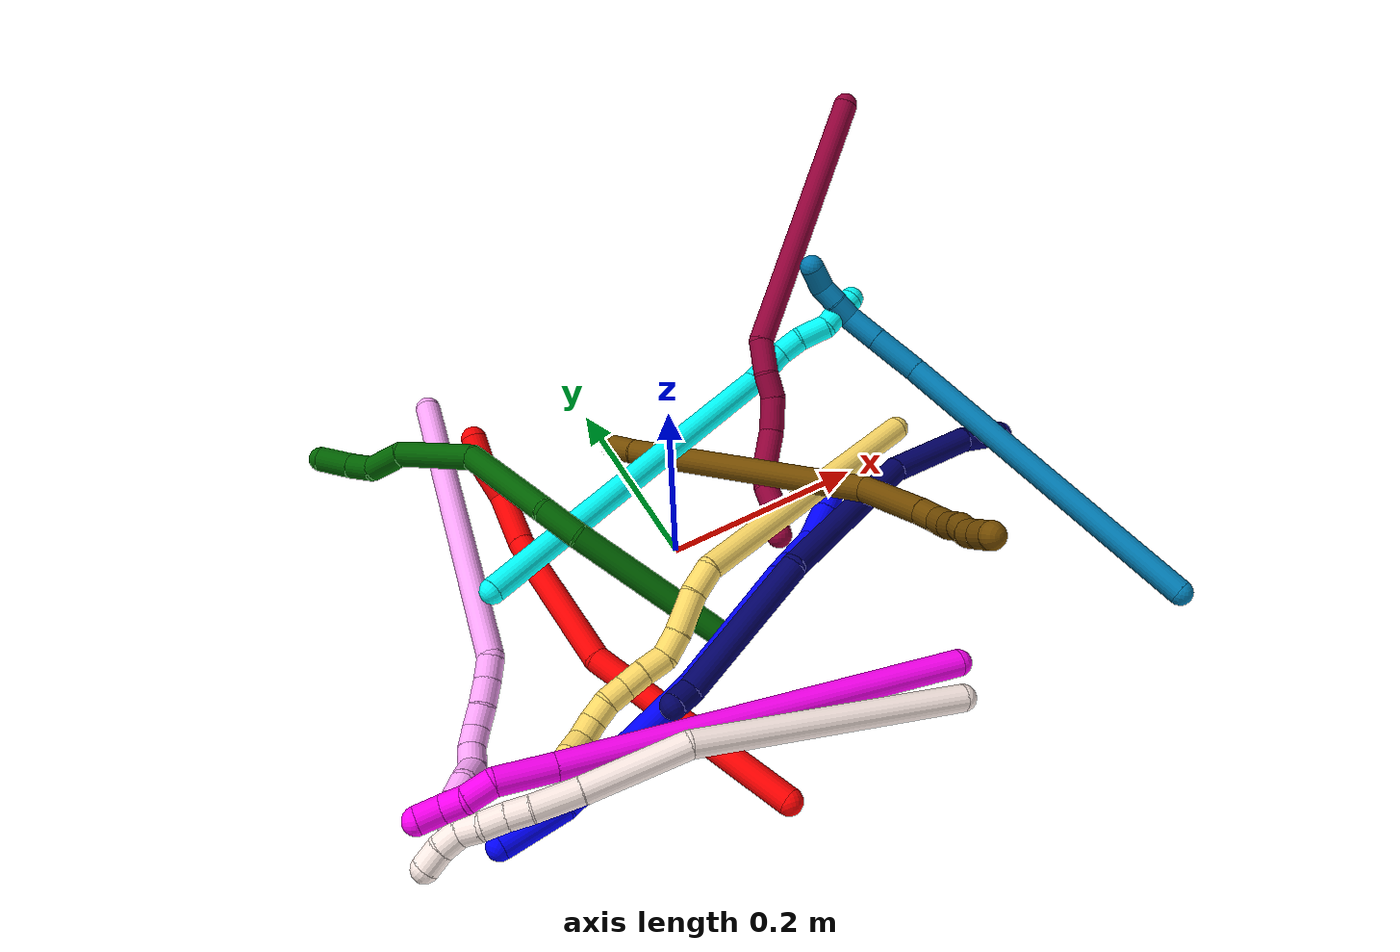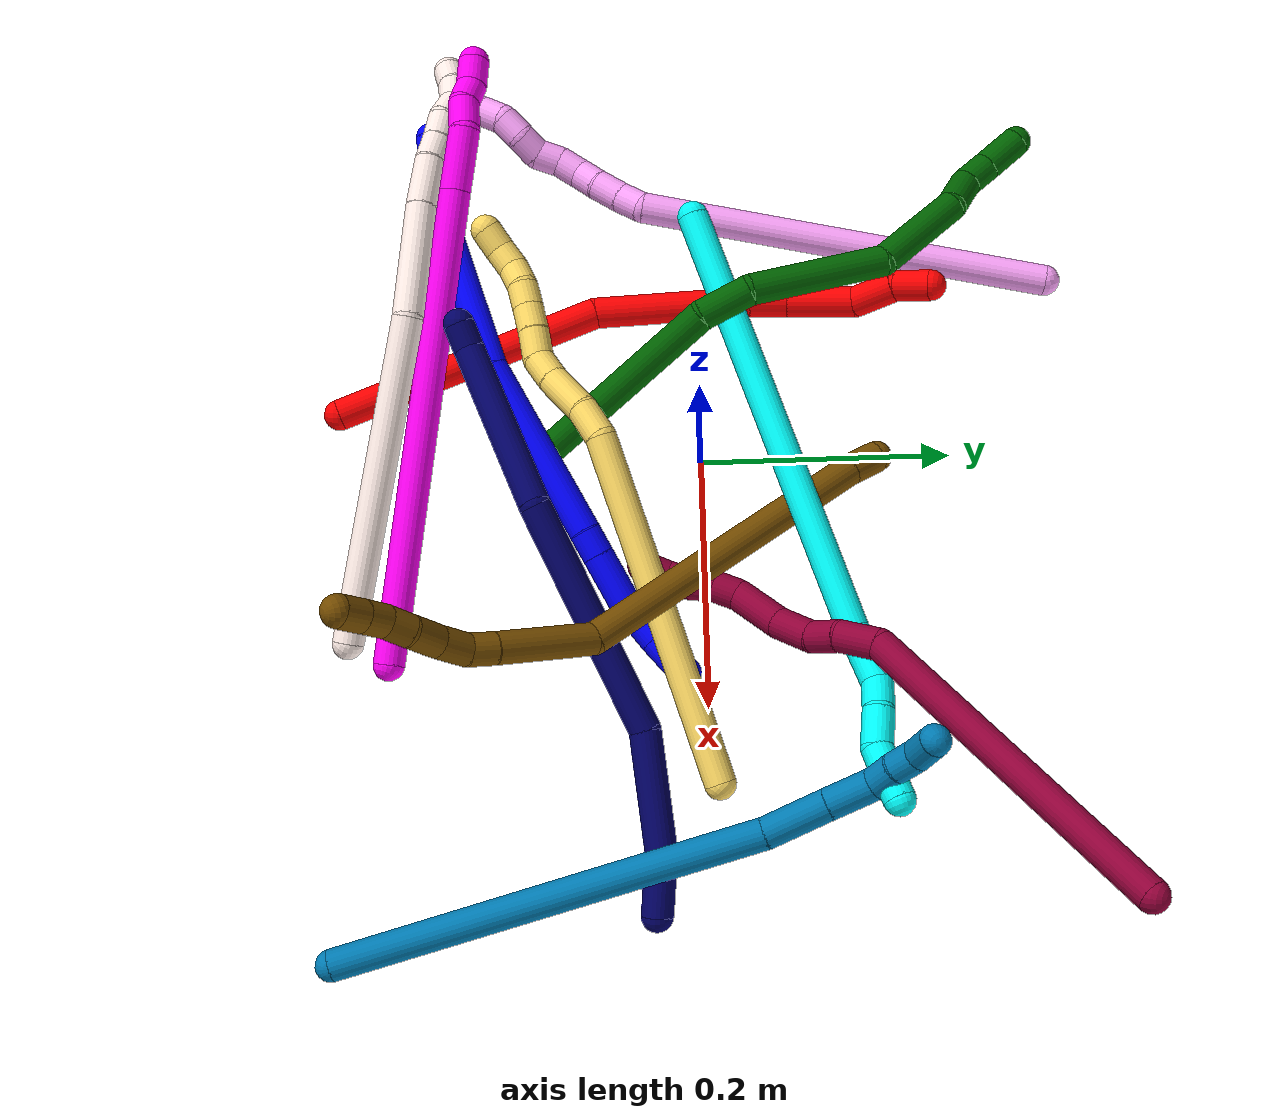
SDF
<sdf version="1.7">
 <world name="default">
  <plugin name="TubeGeneratorPlugin" filename="libtube_generator_plugin.so"/>
  <model name="photoneo_s_sensor">
   <static>1</static>
   <pose>0 0 2 1.57079 1.57079 3.14159</pose>
   <link name="link">
    <inertial><mass>0.1</mass></inertial>
    <sensor name="sensor" type="depth">
     <update_rate>30</update_rate>
     <camera>
      <horizontal_fov>1.22</horizontal_fov>
      <image><width>1920</width><height>1200</height><format>B8G8R8</format></image>
      <clip><near>0.1</near><far>4</far></clip>
      <depth_camera><output>points</output></depth_camera>
     </camera>
     <plugin name="camera_plugin" filename="libgazebo_ros_depth_camera.so">
      <baseline>0.2</baseline>
      <alwaysOn>1</alwaysOn>
      <updateRate>0.0</updateRate>
      <cameraName>camera_ir</cameraName>
      <imageTopicName>/camera/color/image_raw</imageTopicName>
      <cameraInfoTopicName>/camera/color/camera_info</cameraInfoTopicName>
      <depthImageTopicName>/camera/depth/image_raw</depthImageTopicName>
      <depthImageCameraInfoTopicName>/camera/depth/camera_info</depthImageCameraInfoTopicName>
      <pointCloudTopicName>/camera/depth/points</pointCloudTopicName>
      <frameName>fr_optical</frameName>
      <pointCloudCutoff>0.1</pointCloudCutoff>
      <pointCloudCutoffMax>2.0</pointCloudCutoffMax>
      <distortionK1>0</distortionK1>
      <distortionK2>0</distortionK2>
      <distortionK3>0</distortionK3>
      <distortionT1>0</distortionT1>
      <distortionT2>0</distortionT2>
      <CxPrime>0</CxPrime>
      <Cx>0</Cx>
      <Cy>0</Cy>
      <focalLength>0</focalLength>
      <hackBaseline>0</hackBaseline>
     </plugin>
    </sensor>
   </link>
  </model>
  <gravity>0 0 -9.8</gravity>
  <magnetic_field>6e-06 2.3e-05 -4.2e-05</magnetic_field>
  <atmosphere type="adiabatic"/>
  <physics name="default_physics" default="0" type="ode">
   <max_step_size>0.003</max_step_size>
   <real_time_factor>1</real_time_factor>
   <real_time_update_rate>1000</real_time_update_rate>
   <max_contacts>10000</max_contacts>
   <ode>
    <solver>
     <type>quick</type>
     <iters>100</iters>
     <sor>1.3</sor>
     <use_dynamic_moi_rescaling>0</use_dynamic_moi_rescaling>
    </solver>
    <constraints>
     <contact_max_correcting_vel>0</contact_max_correcting_vel>
     <contact_surface_layer>0.001</contact_surface_layer>
     <cfm>0</cfm>
     <erp>0.2</erp>
    </constraints>
   </ode>
  </physics>
  <scene><ambient>0.4 0.4 0.4 1</ambient><background>0.7 0.7 0.7 1</background><shadows>0</shadows></scene>
  <audio><device>default</device></audio>
  <spherical_coordinates>
   <surface_model>EARTH_WGS84</surface_model>
   <latitude_deg>0</latitude_deg>
   <longitude_deg>0</longitude_deg>
   <elevation>0</elevation>
   <heading_deg>0</heading_deg>
  </spherical_coordinates>
  <model name="bin">
   <static>1</static>
   <link name="bottom">
    <collision name="collision-bottom">
     <pose>0 0 -0.01 0 -0 0</pose>
     <geometry><box><size>0.8 0.6 0.02</size></box></geometry>
     <surface>
      <friction><ode><mu>100</mu><mu2>100</mu2></ode></friction>
      <contact><collide_bitmask>65535</collide_bitmask></contact>
     </surface>
    </collision>
   </link>
   <link name="west_wall">
    <collision name="collision-west_wall">
     <pose>-0.41 0 0.1 0 -0 0</pose>
     <geometry><box><size>0.02 0.6 0.2</size></box></geometry>
     <surface>
      <friction><ode><mu>100</mu><mu2>100</mu2></ode></friction>
      <contact><collide_bitmask>65535</collide_bitmask></contact>
     </surface>
    </collision>
   </link>
   <link name="east_wall">
    <collision name="collision-east_wall">
     <pose>0.41 0 0.1 0 -0 0</pose>
     <geometry><box><size>0.02 0.6 0.2</size></box></geometry>
     <surface>
      <friction><ode><mu>100</mu><mu2>100</mu2></ode></friction>
      <contact><collide_bitmask>65535</collide_bitmask></contact>
     </surface>
    </collision>
   </link>
   <link name="south_wall">
    <collision name="collision-south_wall">
     <pose>0 -0.31 0.1 0 -0 0</pose>
     <geometry><box><size>0.8 0.02 0.2</size></box></geometry>
     <surface>
      <friction><ode><mu>100</mu><mu2>100</mu2></ode></friction>
      <contact><collide_bitmask>65535</collide_bitmask></contact>
     </surface>
    </collision>
   </link>
   <link name="north_wall">
    <collision name="collision-north_wall">
     <pose>0 0.31 0.1 0 -0 0</pose>
     <geometry><box><size>0.8 0.02 0.2</size></box></geometry>
     <surface>
      <friction><ode><mu>100</mu><mu2>100</mu2></ode></friction>
      <contact><collide_bitmask>65535</collide_bitmask></contact>
     </surface>
    </collision>
   </link>
  </model>
  <model name="1">
   <static>0</static>
   <link name="1">
    <collision name="collision-cylinder-e_1_1_4">
     <pose>0.006811 0.014128 -0.026412 -2.6504 0.223582 -0.842146</pose>
     <geometry><cylinder><radius>0.0125</radius><length>0.061436</length></cylinder></geometry>
     <surface>
      <friction><ode><mu>1.16</mu><mu2>1.16</mu2><slip1>0</slip1><slip2>0</slip2></ode></friction>
      <contact><ode><kp>1e+06</kp><kd>1</kd><max_vel>0</max_vel><min_depth>0.001</min_depth></ode></contact>
     </surface>
    </collision>
    <visual name="visual-cylinder-e_1_1_4">
     <pose>0.006811 0.014128 -0.026412 -2.6504 0.223582 -0.842146</pose>
     <geometry><cylinder><radius>0.0125</radius><length>0.061436</length></cylinder></geometry>
     <material><ambient>0 0 1 1</ambient></material>
    </visual>
    <collision name="collision-cylinder-e_2_4_5">
     <pose>0.019662 0.052117 -0.123204 -2.81473 0.081095 -0.48247</pose>
     <geometry><cylinder><radius>0.0125</radius><length>0.149119</length></cylinder></geometry>
     <surface>
      <friction><ode><mu>1.16</mu><mu2>1.16</mu2><slip1>0</slip1><slip2>0</slip2></ode></friction>
      <contact><ode><kp>1e+06</kp><kd>1</kd><max_vel>0</max_vel><min_depth>0.001</min_depth></ode></contact>
     </surface>
    </collision>
    <visual name="visual-cylinder-e_2_4_5">
     <pose>0.019662 0.052117 -0.123204 -2.81473 0.081095 -0.48247</pose>
     <geometry><cylinder><radius>0.0125</radius><length>0.149119</length></cylinder></geometry>
     <material><ambient>0 0 1 1</ambient></material>
    </visual>
    <collision name="collision-cylinder-e_3_5_6">
     <pose>0.034975 0.082696 -0.268563 -3.05222 0.122565 -1.88207</pose>
     <geometry><cylinder><radius>0.0125</radius><length>0.151698</length></cylinder></geometry>
     <surface>
      <friction><ode><mu>1.16</mu><mu2>1.16</mu2><slip1>0</slip1><slip2>0</slip2></ode></friction>
      <contact><ode><kp>1e+06</kp><kd>1</kd><max_vel>0</max_vel><min_depth>0.001</min_depth></ode></contact>
     </surface>
    </collision>
    <visual name="visual-cylinder-e_3_5_6">
     <pose>0.034975 0.082696 -0.268563 -3.05222 0.122565 -1.88207</pose>
     <geometry><cylinder><radius>0.0125</radius><length>0.151698</length></cylinder></geometry>
     <material><ambient>0 0 1 1</ambient></material>
    </visual>
    <collision name="collision-cylinder-e_4_6_7">
     <pose>0.046597 0.089692 -0.353831 -3.11467 0.224391 -2.90373</pose>
     <geometry><cylinder><radius>0.0125</radius><length>0.021113</length></cylinder></geometry>
     <surface>
      <friction><ode><mu>1.16</mu><mu2>1.16</mu2><slip1>0</slip1><slip2>0</slip2></ode></friction>
      <contact><ode><kp>1e+06</kp><kd>1</kd><max_vel>0</max_vel><min_depth>0.001</min_depth></ode></contact>
     </surface>
    </collision>
    <visual name="visual-cylinder-e_4_6_7">
     <pose>0.046597 0.089692 -0.353831 -3.11467 0.224391 -2.90373</pose>
     <geometry><cylinder><radius>0.0125</radius><length>0.021113</length></cylinder></geometry>
     <material><ambient>0 0 1 1</ambient></material>
    </visual>
    <collision name="collision-cylinder-e_5_7_8">
     <pose>0.054109 0.090198 -0.384423 -3.13034 0.248986 -3.05176</pose>
     <geometry><cylinder><radius>0.0125</radius><length>0.041903</length></cylinder></geometry>
     <surface>
      <friction><ode><mu>1.16</mu><mu2>1.16</mu2><slip1>0</slip1><slip2>0</slip2></ode></friction>
      <contact><ode><kp>1e+06</kp><kd>1</kd><max_vel>0</max_vel><min_depth>0.001</min_depth></ode></contact>
     </surface>
    </collision>
    <visual name="visual-cylinder-e_5_7_8">
     <pose>0.054109 0.090198 -0.384423 -3.13034 0.248986 -3.05176</pose>
     <geometry><cylinder><radius>0.0125</radius><length>0.041903</length></cylinder></geometry>
     <material><ambient>0 0 1 1</ambient></material>
    </visual>
    <collision name="collision-cylinder-e_6_8_9">
     <pose>0.058661 0.090044 -0.424557 3.12232 -0.03077 -2.02262</pose>
     <geometry><cylinder><radius>0.0125</radius><length>0.039686</length></cylinder></geometry>
     <surface>
      <friction><ode><mu>1.16</mu><mu2>1.16</mu2><slip1>0</slip1><slip2>0</slip2></ode></friction>
      <contact><ode><kp>1e+06</kp><kd>1</kd><max_vel>0</max_vel><min_depth>0.001</min_depth></ode></contact>
     </surface>
    </collision>
    <visual name="visual-cylinder-e_6_8_9">
     <pose>0.058661 0.090044 -0.424557 3.12232 -0.03077 -2.02262</pose>
     <geometry><cylinder><radius>0.0125</radius><length>0.039686</length></cylinder></geometry>
     <material><ambient>0 0 1 1</ambient></material>
    </visual>
    <collision name="collision-cylinder-e_7_9_2">
     <pose>0.056329 0.089189 -0.461818 3.1145 -0.098383 -2.60448</pose>
     <geometry><cylinder><radius>0.0125</radius><length>0.035046</length></cylinder></geometry>
     <surface>
      <friction><ode><mu>1.16</mu><mu2>1.16</mu2><slip1>0</slip1><slip2>0</slip2></ode></friction>
      <contact><ode><kp>1e+06</kp><kd>1</kd><max_vel>0</max_vel><min_depth>0.001</min_depth></ode></contact>
     </surface>
    </collision>
    <visual name="visual-cylinder-e_7_9_2">
     <pose>0.056329 0.089189 -0.461818 3.1145 -0.098383 -2.60448</pose>
     <geometry><cylinder><radius>0.0125</radius><length>0.035046</length></cylinder></geometry>
     <material><ambient>0 0 1 1</ambient></material>
    </visual>
    <collision name="collision-sphere-2">
     <pose>0.054608 0.088717 -0.47925 0 -0 0</pose>
     <geometry><sphere><radius>0.0125</radius></sphere></geometry>
     <surface>
      <friction><ode><mu>1.16</mu><mu2>1.16</mu2><slip1>0</slip1><slip2>0</slip2></ode></friction>
      <contact><ode><kp>1e+06</kp><kd>1</kd><max_vel>0</max_vel><min_depth>0.001</min_depth></ode></contact>
     </surface>
    </collision>
    <visual name="visual-sphere-2">
     <pose>0.054608 0.088717 -0.47925 0 -0 0</pose>
     <geometry><sphere><radius>0.0125</radius></sphere></geometry>
     <material><ambient>0 0 1 1</ambient></material>
    </visual>
    <collision name="collision-sphere-9">
     <pose>0.058051 0.089662 -0.444387 0 -0 0</pose>
     <geometry><sphere><radius>0.0125</radius></sphere></geometry>
     <surface>
      <friction><ode><mu>1.16</mu><mu2>1.16</mu2><slip1>0</slip1><slip2>0</slip2></ode></friction>
      <contact><ode><kp>1e+06</kp><kd>1</kd><max_vel>0</max_vel><min_depth>0.001</min_depth></ode></contact>
     </surface>
    </collision>
    <visual name="visual-sphere-9">
     <pose>0.058051 0.089662 -0.444387 0 -0 0</pose>
     <geometry><sphere><radius>0.0125</radius></sphere></geometry>
     <material><ambient>0 0 1 1</ambient></material>
    </visual>
    <collision name="collision-sphere-4">
     <pose>0.013622 0.028257 -0.052824 0 -0 0</pose>
     <geometry><sphere><radius>0.0125</radius></sphere></geometry>
     <surface>
      <friction><ode><mu>1.16</mu><mu2>1.16</mu2><slip1>0</slip1><slip2>0</slip2></ode></friction>
      <contact><ode><kp>1e+06</kp><kd>1</kd><max_vel>0</max_vel><min_depth>0.001</min_depth></ode></contact>
     </surface>
    </collision>
    <visual name="visual-sphere-4">
     <pose>0.013622 0.028257 -0.052824 0 -0 0</pose>
     <geometry><sphere><radius>0.0125</radius></sphere></geometry>
     <material><ambient>0 0 1 1</ambient></material>
    </visual>
    <collision name="collision-sphere-1">
     <geometry><sphere><radius>0.0125</radius></sphere></geometry>
     <surface>
      <friction><ode><mu>1.16</mu><mu2>1.16</mu2><slip1>0</slip1><slip2>0</slip2></ode></friction>
      <contact><ode><kp>1e+06</kp><kd>1</kd><max_vel>0</max_vel><min_depth>0.001</min_depth></ode></contact>
     </surface>
    </collision>
    <visual name="visual-sphere-1">
     <geometry><sphere><radius>0.0125</radius></sphere></geometry>
     <material><ambient>0 0 1 1</ambient></material>
    </visual>
    <collision name="collision-sphere-8">
     <pose>0.059272 0.090426 -0.404727 0 -0 0</pose>
     <geometry><sphere><radius>0.0125</radius></sphere></geometry>
     <surface>
      <friction><ode><mu>1.16</mu><mu2>1.16</mu2><slip1>0</slip1><slip2>0</slip2></ode></friction>
      <contact><ode><kp>1e+06</kp><kd>1</kd><max_vel>0</max_vel><min_depth>0.001</min_depth></ode></contact>
     </surface>
    </collision>
    <visual name="visual-sphere-8">
     <pose>0.059272 0.090426 -0.404727 0 -0 0</pose>
     <geometry><sphere><radius>0.0125</radius></sphere></geometry>
     <material><ambient>0 0 1 1</ambient></material>
    </visual>
    <collision name="collision-sphere-5">
     <pose>0.025701 0.075977 -0.193583 0 -0 0</pose>
     <geometry><sphere><radius>0.0125</radius></sphere></geometry>
     <surface>
      <friction><ode><mu>1.16</mu><mu2>1.16</mu2><slip1>0</slip1><slip2>0</slip2></ode></friction>
      <contact><ode><kp>1e+06</kp><kd>1</kd><max_vel>0</max_vel><min_depth>0.001</min_depth></ode></contact>
     </surface>
    </collision>
    <visual name="visual-sphere-5">
     <pose>0.025701 0.075977 -0.193583 0 -0 0</pose>
     <geometry><sphere><radius>0.0125</radius></sphere></geometry>
     <material><ambient>0 0 1 1</ambient></material>
    </visual>
    <collision name="collision-sphere-6">
     <pose>0.044248 0.089415 -0.343543 0 -0 0</pose>
     <geometry><sphere><radius>0.0125</radius></sphere></geometry>
     <surface>
      <friction><ode><mu>1.16</mu><mu2>1.16</mu2><slip1>0</slip1><slip2>0</slip2></ode></friction>
      <contact><ode><kp>1e+06</kp><kd>1</kd><max_vel>0</max_vel><min_depth>0.001</min_depth></ode></contact>
     </surface>
    </collision>
    <visual name="visual-sphere-6">
     <pose>0.044248 0.089415 -0.343543 0 -0 0</pose>
     <geometry><sphere><radius>0.0125</radius></sphere></geometry>
     <material><ambient>0 0 1 1</ambient></material>
    </visual>
    <collision name="collision-sphere-7">
     <pose>0.048946 0.089969 -0.364119 0 -0 0</pose>
     <geometry><sphere><radius>0.0125</radius></sphere></geometry>
     <surface>
      <friction><ode><mu>1.16</mu><mu2>1.16</mu2><slip1>0</slip1><slip2>0</slip2></ode></friction>
      <contact><ode><kp>1e+06</kp><kd>1</kd><max_vel>0</max_vel><min_depth>0.001</min_depth></ode></contact>
     </surface>
    </collision>
    <visual name="visual-sphere-7">
     <pose>0.048946 0.089969 -0.364119 0 -0 0</pose>
     <geometry><sphere><radius>0.0125</radius></sphere></geometry>
     <material><ambient>0 0 1 1</ambient></material>
    </visual>
    <inertial>
     <pose>0.032418 0.067114 -0.234695 0 -0 0</pose>
     <mass>0.5</mass>
     <inertia>
      <ixx>-0.000275</ixx>
      <ixy>0</ixy>
      <ixz>0</ixz>
      <iyy>-0.000564</iyy>
      <iyz>0</iyz>
      <izz>-0.000229</izz>
     </inertia>
    </inertial>
   </link>
   <pose>-0.275324 -0.213417 0.031388 1.51904 1.0675 -0.989179</pose>
  </model>
  <model name="2">
   <static>0</static>
   <link name="2">
    <collision name="collision-cylinder-e_1_1_4">
     <pose>-0.018176 0.059608 -0.091629 -2.56485 -0.164773 0.542975</pose>
     <geometry><cylinder><radius>0.0125</radius><length>0.221625</length></cylinder></geometry>
     <surface>
      <friction><ode><mu>1.16</mu><mu2>1.16</mu2><slip1>0</slip1><slip2>0</slip2></ode></friction>
      <contact><ode><kp>1e+06</kp><kd>1</kd><max_vel>0</max_vel><min_depth>0.001</min_depth></ode></contact>
     </surface>
    </collision>
    <visual name="visual-cylinder-e_1_1_4">
     <pose>-0.018176 0.059608 -0.091629 -2.56485 -0.164773 0.542975</pose>
     <geometry><cylinder><radius>0.0125</radius><length>0.221625</length></cylinder></geometry>
     <material><ambient>1 0 0 1</ambient></material>
    </visual>
    <collision name="collision-cylinder-e_2_4_5">
     <pose>-0.05056 0.134498 -0.242019 -2.88715 -0.229863 1.46839</pose>
     <geometry><cylinder><radius>0.0125</radius><length>0.12471</length></cylinder></geometry>
     <surface>
      <friction><ode><mu>1.16</mu><mu2>1.16</mu2><slip1>0</slip1><slip2>0</slip2></ode></friction>
      <contact><ode><kp>1e+06</kp><kd>1</kd><max_vel>0</max_vel><min_depth>0.001</min_depth></ode></contact>
     </surface>
    </collision>
    <visual name="visual-cylinder-e_2_4_5">
     <pose>-0.05056 0.134498 -0.242019 -2.88715 -0.229863 1.46839</pose>
     <geometry><cylinder><radius>0.0125</radius><length>0.12471</length></cylinder></geometry>
     <material><ambient>1 0 0 1</ambient></material>
    </visual>
    <collision name="collision-cylinder-e_3_5_6">
     <pose>-0.069348 0.152866 -0.315447 -2.9342 -0.29655 1.92457</pose>
     <geometry><cylinder><radius>0.0125</radius><length>0.031348</length></cylinder></geometry>
     <surface>
      <friction><ode><mu>1.16</mu><mu2>1.16</mu2><slip1>0</slip1><slip2>0</slip2></ode></friction>
      <contact><ode><kp>1e+06</kp><kd>1</kd><max_vel>0</max_vel><min_depth>0.001</min_depth></ode></contact>
     </surface>
    </collision>
    <visual name="visual-cylinder-e_3_5_6">
     <pose>-0.069348 0.152866 -0.315447 -2.9342 -0.29655 1.92457</pose>
     <geometry><cylinder><radius>0.0125</radius><length>0.031348</length></cylinder></geometry>
     <material><ambient>1 0 0 1</ambient></material>
    </visual>
    <collision name="collision-cylinder-e_4_6_7">
     <pose>-0.075839 0.158396 -0.357921 -3.05393 -0.068382 1.3247</pose>
     <geometry><cylinder><radius>0.0125</radius><length>0.055955</length></cylinder></geometry>
     <surface>
      <friction><ode><mu>1.16</mu><mu2>1.16</mu2><slip1>0</slip1><slip2>0</slip2></ode></friction>
      <contact><ode><kp>1e+06</kp><kd>1</kd><max_vel>0</max_vel><min_depth>0.001</min_depth></ode></contact>
     </surface>
    </collision>
    <visual name="visual-cylinder-e_4_6_7">
     <pose>-0.075839 0.158396 -0.357921 -3.05393 -0.068382 1.3247</pose>
     <geometry><cylinder><radius>0.0125</radius><length>0.055955</length></cylinder></geometry>
     <material><ambient>1 0 0 1</ambient></material>
    </visual>
    <collision name="collision-cylinder-e_5_7_8">
     <pose>-0.071465 0.165715 -0.402671 -2.86147 0.342465 -1.77361</pose>
     <geometry><cylinder><radius>0.0125</radius><length>0.03744</length></cylinder></geometry>
     <surface>
      <friction><ode><mu>1.16</mu><mu2>1.16</mu2><slip1>0</slip1><slip2>0</slip2></ode></friction>
      <contact><ode><kp>1e+06</kp><kd>1</kd><max_vel>0</max_vel><min_depth>0.001</min_depth></ode></contact>
     </surface>
    </collision>
    <visual name="visual-cylinder-e_5_7_8">
     <pose>-0.071465 0.165715 -0.402671 -2.86147 0.342465 -1.77361</pose>
     <geometry><cylinder><radius>0.0125</radius><length>0.03744</length></cylinder></geometry>
     <material><ambient>1 0 0 1</ambient></material>
    </visual>
    <collision name="collision-cylinder-e_6_8_2">
     <pose>-0.064114 0.171036 -0.434032 -3.11069 0.073638 -2.3472</pose>
     <geometry><cylinder><radius>0.0125</radius><length>0.028923</length></cylinder></geometry>
     <surface>
      <friction><ode><mu>1.16</mu><mu2>1.16</mu2><slip1>0</slip1><slip2>0</slip2></ode></friction>
      <contact><ode><kp>1e+06</kp><kd>1</kd><max_vel>0</max_vel><min_depth>0.001</min_depth></ode></contact>
     </surface>
    </collision>
    <visual name="visual-cylinder-e_6_8_2">
     <pose>-0.064114 0.171036 -0.434032 -3.11069 0.073638 -2.3472</pose>
     <geometry><cylinder><radius>0.0125</radius><length>0.028923</length></cylinder></geometry>
     <material><ambient>1 0 0 1</ambient></material>
    </visual>
    <collision name="collision-sphere-2">
     <pose>-0.06305 0.171481 -0.448447 0 -0 0</pose>
     <geometry><sphere><radius>0.0125</radius></sphere></geometry>
     <surface>
      <friction><ode><mu>1.16</mu><mu2>1.16</mu2><slip1>0</slip1><slip2>0</slip2></ode></friction>
      <contact><ode><kp>1e+06</kp><kd>1</kd><max_vel>0</max_vel><min_depth>0.001</min_depth></ode></contact>
     </surface>
    </collision>
    <visual name="visual-sphere-2">
     <pose>-0.06305 0.171481 -0.448447 0 -0 0</pose>
     <geometry><sphere><radius>0.0125</radius></sphere></geometry>
     <material><ambient>1 0 0 1</ambient></material>
    </visual>
    <collision name="collision-sphere-4">
     <pose>-0.036353 0.119215 -0.183259 0 -0 0</pose>
     <geometry><sphere><radius>0.0125</radius></sphere></geometry>
     <surface>
      <friction><ode><mu>1.16</mu><mu2>1.16</mu2><slip1>0</slip1><slip2>0</slip2></ode></friction>
      <contact><ode><kp>1e+06</kp><kd>1</kd><max_vel>0</max_vel><min_depth>0.001</min_depth></ode></contact>
     </surface>
    </collision>
    <visual name="visual-sphere-4">
     <pose>-0.036353 0.119215 -0.183259 0 -0 0</pose>
     <geometry><sphere><radius>0.0125</radius></sphere></geometry>
     <material><ambient>1 0 0 1</ambient></material>
    </visual>
    <collision name="collision-sphere-1">
     <geometry><sphere><radius>0.0125</radius></sphere></geometry>
     <surface>
      <friction><ode><mu>1.16</mu><mu2>1.16</mu2><slip1>0</slip1><slip2>0</slip2></ode></friction>
      <contact><ode><kp>1e+06</kp><kd>1</kd><max_vel>0</max_vel><min_depth>0.001</min_depth></ode></contact>
     </surface>
    </collision>
    <visual name="visual-sphere-1">
     <geometry><sphere><radius>0.0125</radius></sphere></geometry>
     <material><ambient>1 0 0 1</ambient></material>
    </visual>
    <collision name="collision-sphere-8">
     <pose>-0.065178 0.17059 -0.419617 0 -0 0</pose>
     <geometry><sphere><radius>0.0125</radius></sphere></geometry>
     <surface>
      <friction><ode><mu>1.16</mu><mu2>1.16</mu2><slip1>0</slip1><slip2>0</slip2></ode></friction>
      <contact><ode><kp>1e+06</kp><kd>1</kd><max_vel>0</max_vel><min_depth>0.001</min_depth></ode></contact>
     </surface>
    </collision>
    <visual name="visual-sphere-8">
     <pose>-0.065178 0.17059 -0.419617 0 -0 0</pose>
     <geometry><sphere><radius>0.0125</radius></sphere></geometry>
     <material><ambient>1 0 0 1</ambient></material>
    </visual>
    <collision name="collision-sphere-5">
     <pose>-0.064767 0.14978 -0.300779 0 -0 0</pose>
     <geometry><sphere><radius>0.0125</radius></sphere></geometry>
     <surface>
      <friction><ode><mu>1.16</mu><mu2>1.16</mu2><slip1>0</slip1><slip2>0</slip2></ode></friction>
      <contact><ode><kp>1e+06</kp><kd>1</kd><max_vel>0</max_vel><min_depth>0.001</min_depth></ode></contact>
     </surface>
    </collision>
    <visual name="visual-sphere-5">
     <pose>-0.064767 0.14978 -0.300779 0 -0 0</pose>
     <geometry><sphere><radius>0.0125</radius></sphere></geometry>
     <material><ambient>1 0 0 1</ambient></material>
    </visual>
    <collision name="collision-sphere-6">
     <pose>-0.073928 0.155953 -0.330116 0 -0 0</pose>
     <geometry><sphere><radius>0.0125</radius></sphere></geometry>
     <surface>
      <friction><ode><mu>1.16</mu><mu2>1.16</mu2><slip1>0</slip1><slip2>0</slip2></ode></friction>
      <contact><ode><kp>1e+06</kp><kd>1</kd><max_vel>0</max_vel><min_depth>0.001</min_depth></ode></contact>
     </surface>
    </collision>
    <visual name="visual-sphere-6">
     <pose>-0.073928 0.155953 -0.330116 0 -0 0</pose>
     <geometry><sphere><radius>0.0125</radius></sphere></geometry>
     <material><ambient>1 0 0 1</ambient></material>
    </visual>
    <collision name="collision-sphere-7">
     <pose>-0.077751 0.16084 -0.385725 0 -0 0</pose>
     <geometry><sphere><radius>0.0125</radius></sphere></geometry>
     <surface>
      <friction><ode><mu>1.16</mu><mu2>1.16</mu2><slip1>0</slip1><slip2>0</slip2></ode></friction>
      <contact><ode><kp>1e+06</kp><kd>1</kd><max_vel>0</max_vel><min_depth>0.001</min_depth></ode></contact>
     </surface>
    </collision>
    <visual name="visual-sphere-7">
     <pose>-0.077751 0.16084 -0.385725 0 -0 0</pose>
     <geometry><sphere><radius>0.0125</radius></sphere></geometry>
     <material><ambient>1 0 0 1</ambient></material>
    </visual>
    <inertial>
     <pose>-0.042562 0.10958 -0.21607 0 -0 0</pose>
     <mass>0.5</mass>
     <inertia>
      <ixx>0.001425</ixx>
      <ixy>0</ixy>
      <ixz>0</ixz>
      <iyy>3.3e-05</iyy>
      <iyz>0</iyz>
      <izz>-0.000384</izz>
     </inertia>
    </inertial>
   </link>
   <pose>-0.044936 -0.288446 0.012255 -2.819 -1.29795 -2.08427</pose>
  </model>
  <model name="3">
   <static>0</static>
   <link name="3">
    <collision name="collision-cylinder-e_1_1_4">
     <pose>0.004466 0.000245 0.177724 -0.001377 0.025125 -1.7e-05</pose>
     <geometry><cylinder><radius>0.0125</radius><length>0.35556</length></cylinder></geometry>
     <surface>
      <friction><ode><mu>1.16</mu><mu2>1.16</mu2><slip1>0</slip1><slip2>0</slip2></ode></friction>
      <contact><ode><kp>1e+06</kp><kd>1</kd><max_vel>0</max_vel><min_depth>0.001</min_depth></ode></contact>
     </surface>
    </collision>
    <visual name="visual-cylinder-e_1_1_4">
     <pose>0.004466 0.000245 0.177724 -0.001377 0.025125 -1.7e-05</pose>
     <geometry><cylinder><radius>0.0125</radius><length>0.35556</length></cylinder></geometry>
     <material><ambient>0.003922 1 0.996078 1</ambient></material>
    </visual>
    <collision name="collision-cylinder-e_2_4_5">
     <pose>0.01314 -0.001488 0.37801 0.087393 0.183687 0.008054</pose>
     <geometry><cylinder><radius>0.0125</radius><length>0.046073</length></cylinder></geometry>
     <surface>
      <friction><ode><mu>1.16</mu><mu2>1.16</mu2><slip1>0</slip1><slip2>0</slip2></ode></friction>
      <contact><ode><kp>1e+06</kp><kd>1</kd><max_vel>0</max_vel><min_depth>0.001</min_depth></ode></contact>
     </surface>
    </collision>
    <visual name="visual-cylinder-e_2_4_5">
     <pose>0.01314 -0.001488 0.37801 0.087393 0.183687 0.008054</pose>
     <geometry><cylinder><radius>0.0125</radius><length>0.046073</length></cylinder></geometry>
     <material><ambient>0.003922 1 0.996078 1</ambient></material>
    </visual>
    <collision name="collision-cylinder-e_3_5_6">
     <pose>0.024463 -0.001604 0.41077 -0.180479 0.601514 -0.056116</pose>
     <geometry><cylinder><radius>0.0125</radius><length>0.025146</length></cylinder></geometry>
     <surface>
      <friction><ode><mu>1.16</mu><mu2>1.16</mu2><slip1>0</slip1><slip2>0</slip2></ode></friction>
      <contact><ode><kp>1e+06</kp><kd>1</kd><max_vel>0</max_vel><min_depth>0.001</min_depth></ode></contact>
     </surface>
    </collision>
    <visual name="visual-cylinder-e_3_5_6">
     <pose>0.024463 -0.001604 0.41077 -0.180479 0.601514 -0.056116</pose>
     <geometry><cylinder><radius>0.0125</radius><length>0.025146</length></cylinder></geometry>
     <material><ambient>0.003922 1 0.996078 1</ambient></material>
    </visual>
    <collision name="collision-cylinder-e_4_6_7">
     <pose>0.037156 0.004991 0.43415 -0.34481 0.378977 -0.066769</pose>
     <geometry><cylinder><radius>0.0125</radius><length>0.030152</length></cylinder></geometry>
     <surface>
      <friction><ode><mu>1.16</mu><mu2>1.16</mu2><slip1>0</slip1><slip2>0</slip2></ode></friction>
      <contact><ode><kp>1e+06</kp><kd>1</kd><max_vel>0</max_vel><min_depth>0.001</min_depth></ode></contact>
     </surface>
    </collision>
    <visual name="visual-cylinder-e_4_6_7">
     <pose>0.037156 0.004991 0.43415 -0.34481 0.378977 -0.066769</pose>
     <geometry><cylinder><radius>0.0125</radius><length>0.030152</length></cylinder></geometry>
     <material><ambient>0.003922 1 0.996078 1</ambient></material>
    </visual>
    <collision name="collision-cylinder-e_5_7_8">
     <pose>0.045746 0.008811 0.457 0.094371 0.300785 0.014311</pose>
     <geometry><cylinder><radius>0.0125</radius><length>0.020335</length></cylinder></geometry>
     <surface>
      <friction><ode><mu>1.16</mu><mu2>1.16</mu2><slip1>0</slip1><slip2>0</slip2></ode></friction>
      <contact><ode><kp>1e+06</kp><kd>1</kd><max_vel>0</max_vel><min_depth>0.001</min_depth></ode></contact>
     </surface>
    </collision>
    <visual name="visual-cylinder-e_5_7_8">
     <pose>0.045746 0.008811 0.457 0.094371 0.300785 0.014311</pose>
     <geometry><cylinder><radius>0.0125</radius><length>0.020335</length></cylinder></geometry>
     <material><ambient>0.003922 1 0.996078 1</ambient></material>
    </visual>
    <collision name="collision-cylinder-e_6_8_2">
     <pose>0.050987 0.006859 0.477766 0.093105 0.197377 0.009225</pose>
     <geometry><cylinder><radius>0.0125</radius><length>0.022734</length></cylinder></geometry>
     <surface>
      <friction><ode><mu>1.16</mu><mu2>1.16</mu2><slip1>0</slip1><slip2>0</slip2></ode></friction>
      <contact><ode><kp>1e+06</kp><kd>1</kd><max_vel>0</max_vel><min_depth>0.001</min_depth></ode></contact>
     </surface>
    </collision>
    <visual name="visual-cylinder-e_6_8_2">
     <pose>0.050987 0.006859 0.477766 0.093105 0.197377 0.009225</pose>
     <geometry><cylinder><radius>0.0125</radius><length>0.022734</length></cylinder></geometry>
     <material><ambient>0.003922 1 0.996078 1</ambient></material>
    </visual>
    <collision name="collision-sphere-2">
     <pose>0.053216 0.005823 0.488864 0 -0 0</pose>
     <geometry><sphere><radius>0.0125</radius></sphere></geometry>
     <surface>
      <friction><ode><mu>1.16</mu><mu2>1.16</mu2><slip1>0</slip1><slip2>0</slip2></ode></friction>
      <contact><ode><kp>1e+06</kp><kd>1</kd><max_vel>0</max_vel><min_depth>0.001</min_depth></ode></contact>
     </surface>
    </collision>
    <visual name="visual-sphere-2">
     <pose>0.053216 0.005823 0.488864 0 -0 0</pose>
     <geometry><sphere><radius>0.0125</radius></sphere></geometry>
     <material><ambient>0.003922 1 0.996078 1</ambient></material>
    </visual>
    <collision name="collision-sphere-4">
     <pose>0.008933 0.000489 0.355447 0 -0 0</pose>
     <geometry><sphere><radius>0.0125</radius></sphere></geometry>
     <surface>
      <friction><ode><mu>1.16</mu><mu2>1.16</mu2><slip1>0</slip1><slip2>0</slip2></ode></friction>
      <contact><ode><kp>1e+06</kp><kd>1</kd><max_vel>0</max_vel><min_depth>0.001</min_depth></ode></contact>
     </surface>
    </collision>
    <visual name="visual-sphere-4">
     <pose>0.008933 0.000489 0.355447 0 -0 0</pose>
     <geometry><sphere><radius>0.0125</radius></sphere></geometry>
     <material><ambient>0.003922 1 0.996078 1</ambient></material>
    </visual>
    <collision name="collision-sphere-1">
     <geometry><sphere><radius>0.0125</radius></sphere></geometry>
     <surface>
      <friction><ode><mu>1.16</mu><mu2>1.16</mu2><slip1>0</slip1><slip2>0</slip2></ode></friction>
      <contact><ode><kp>1e+06</kp><kd>1</kd><max_vel>0</max_vel><min_depth>0.001</min_depth></ode></contact>
     </surface>
    </collision>
    <visual name="visual-sphere-1">
     <geometry><sphere><radius>0.0125</radius></sphere></geometry>
     <material><ambient>0.003922 1 0.996078 1</ambient></material>
    </visual>
    <collision name="collision-sphere-8">
     <pose>0.048758 0.007896 0.466668 0 -0 0</pose>
     <geometry><sphere><radius>0.0125</radius></sphere></geometry>
     <surface>
      <friction><ode><mu>1.16</mu><mu2>1.16</mu2><slip1>0</slip1><slip2>0</slip2></ode></friction>
      <contact><ode><kp>1e+06</kp><kd>1</kd><max_vel>0</max_vel><min_depth>0.001</min_depth></ode></contact>
     </surface>
    </collision>
    <visual name="visual-sphere-8">
     <pose>0.048758 0.007896 0.466668 0 -0 0</pose>
     <geometry><sphere><radius>0.0125</radius></sphere></geometry>
     <material><ambient>0.003922 1 0.996078 1</ambient></material>
    </visual>
    <collision name="collision-sphere-5">
     <pose>0.017348 -0.003464 0.400573 0 -0 0</pose>
     <geometry><sphere><radius>0.0125</radius></sphere></geometry>
     <surface>
      <friction><ode><mu>1.16</mu><mu2>1.16</mu2><slip1>0</slip1><slip2>0</slip2></ode></friction>
      <contact><ode><kp>1e+06</kp><kd>1</kd><max_vel>0</max_vel><min_depth>0.001</min_depth></ode></contact>
     </surface>
    </collision>
    <visual name="visual-sphere-5">
     <pose>0.017348 -0.003464 0.400573 0 -0 0</pose>
     <geometry><sphere><radius>0.0125</radius></sphere></geometry>
     <material><ambient>0.003922 1 0.996078 1</ambient></material>
    </visual>
    <collision name="collision-sphere-6">
     <pose>0.031578 0.000257 0.420968 0 -0 0</pose>
     <geometry><sphere><radius>0.0125</radius></sphere></geometry>
     <surface>
      <friction><ode><mu>1.16</mu><mu2>1.16</mu2><slip1>0</slip1><slip2>0</slip2></ode></friction>
      <contact><ode><kp>1e+06</kp><kd>1</kd><max_vel>0</max_vel><min_depth>0.001</min_depth></ode></contact>
     </surface>
    </collision>
    <visual name="visual-sphere-6">
     <pose>0.031578 0.000257 0.420968 0 -0 0</pose>
     <geometry><sphere><radius>0.0125</radius></sphere></geometry>
     <material><ambient>0.003922 1 0.996078 1</ambient></material>
    </visual>
    <collision name="collision-sphere-7">
     <pose>0.042733 0.009726 0.447332 0 -0 0</pose>
     <geometry><sphere><radius>0.0125</radius></sphere></geometry>
     <surface>
      <friction><ode><mu>1.16</mu><mu2>1.16</mu2><slip1>0</slip1><slip2>0</slip2></ode></friction>
      <contact><ode><kp>1e+06</kp><kd>1</kd><max_vel>0</max_vel><min_depth>0.001</min_depth></ode></contact>
     </surface>
    </collision>
    <visual name="visual-sphere-7">
     <pose>0.042733 0.009726 0.447332 0 -0 0</pose>
     <geometry><sphere><radius>0.0125</radius></sphere></geometry>
     <material><ambient>0.003922 1 0.996078 1</ambient></material>
    </visual>
    <inertial>
     <pose>0.012037 0.000927 0.248364 0 -0 0</pose>
     <mass>0.5</mass>
     <inertia>
      <ixx>0.003781</ixx>
      <ixy>0</ixy>
      <ixz>0</ixz>
      <iyy>0.003779</iyy>
      <iyz>0</iyz>
      <izz>-6.7e-05</izz>
     </inertia>
    </inertial>
   </link>
   <pose>-0.185619 -0.000401 0.0641 -1.70533 -1.23285 -1.11351</pose>
  </model>
  <model name="4">
   <static>0</static>
   <link name="4">
    <collision name="collision-cylinder-e_1_1_4">
     <pose>-0.041162 -0.103987 -0.12363 2.44228 -0.249488 -0.662437</pose>
     <geometry><cylinder><radius>0.0125</radius><length>0.333418</length></cylinder></geometry>
     <surface>
      <friction><ode><mu>1.16</mu><mu2>1.16</mu2><slip1>0</slip1><slip2>0</slip2></ode></friction>
      <contact><ode><kp>1e+06</kp><kd>1</kd><max_vel>0</max_vel><min_depth>0.001</min_depth></ode></contact>
     </surface>
    </collision>
    <visual name="visual-cylinder-e_1_1_4">
     <pose>-0.041162 -0.103987 -0.12363 2.44228 -0.249488 -0.662437</pose>
     <geometry><cylinder><radius>0.0125</radius><length>0.333418</length></cylinder></geometry>
     <material><ambient>1 0.65098 0.996078 1</ambient></material>
    </visual>
    <collision name="collision-cylinder-e_2_4_5">
     <pose>-0.08625 -0.217264 -0.250692 1.92477 -0.377461 -0.535266</pose>
     <geometry><cylinder><radius>0.0125</radius><length>0.021306</length></cylinder></geometry>
     <surface>
      <friction><ode><mu>1.16</mu><mu2>1.16</mu2><slip1>0</slip1><slip2>0</slip2></ode></friction>
      <contact><ode><kp>1e+06</kp><kd>1</kd><max_vel>0</max_vel><min_depth>0.001</min_depth></ode></contact>
     </surface>
    </collision>
    <visual name="visual-cylinder-e_2_4_5">
     <pose>-0.08625 -0.217264 -0.250692 1.92477 -0.377461 -0.535266</pose>
     <geometry><cylinder><radius>0.0125</radius><length>0.021306</length></cylinder></geometry>
     <material><ambient>1 0.65098 0.996078 1</ambient></material>
    </visual>
    <collision name="collision-cylinder-e_3_5_6">
     <pose>-0.093375 -0.237307 -0.258477 1.95536 -0.269014 -0.396242</pose>
     <geometry><cylinder><radius>0.0125</radius><length>0.024068</length></cylinder></geometry>
     <surface>
      <friction><ode><mu>1.16</mu><mu2>1.16</mu2><slip1>0</slip1><slip2>0</slip2></ode></friction>
      <contact><ode><kp>1e+06</kp><kd>1</kd><max_vel>0</max_vel><min_depth>0.001</min_depth></ode></contact>
     </surface>
    </collision>
    <visual name="visual-cylinder-e_3_5_6">
     <pose>-0.093375 -0.237307 -0.258477 1.95536 -0.269014 -0.396242</pose>
     <geometry><cylinder><radius>0.0125</radius><length>0.024068</length></cylinder></geometry>
     <material><ambient>1 0.65098 0.996078 1</ambient></material>
    </visual>
    <collision name="collision-cylinder-e_4_6_7">
     <pose>-0.100071 -0.257595 -0.264959 1.79058 -0.343861 -0.426831</pose>
     <geometry><cylinder><radius>0.0125</radius><length>0.020753</length></cylinder></geometry>
     <surface>
      <friction><ode><mu>1.16</mu><mu2>1.16</mu2><slip1>0</slip1><slip2>0</slip2></ode></friction>
      <contact><ode><kp>1e+06</kp><kd>1</kd><max_vel>0</max_vel><min_depth>0.001</min_depth></ode></contact>
     </surface>
    </collision>
    <visual name="visual-cylinder-e_4_6_7">
     <pose>-0.100071 -0.257595 -0.264959 1.79058 -0.343861 -0.426831</pose>
     <geometry><cylinder><radius>0.0125</radius><length>0.020753</length></cylinder></geometry>
     <material><ambient>1 0.65098 0.996078 1</ambient></material>
    </visual>
    <collision name="collision-cylinder-e_5_7_8">
     <pose>-0.104643 -0.27593 -0.271862 2.06769 -0.10683 -0.179149</pose>
     <geometry><cylinder><radius>0.0125</radius><length>0.020138</length></cylinder></geometry>
     <surface>
      <friction><ode><mu>1.16</mu><mu2>1.16</mu2><slip1>0</slip1><slip2>0</slip2></ode></friction>
      <contact><ode><kp>1e+06</kp><kd>1</kd><max_vel>0</max_vel><min_depth>0.001</min_depth></ode></contact>
     </surface>
    </collision>
    <visual name="visual-cylinder-e_5_7_8">
     <pose>-0.104643 -0.27593 -0.271862 2.06769 -0.10683 -0.179149</pose>
     <geometry><cylinder><radius>0.0125</radius><length>0.020138</length></cylinder></geometry>
     <material><ambient>1 0.65098 0.996078 1</ambient></material>
    </visual>
    <collision name="collision-cylinder-e_6_8_9">
     <pose>-0.106759 -0.29168 -0.283902 2.37863 -0.103317 -0.256378</pose>
     <geometry><cylinder><radius>0.0125</radius><length>0.020218</length></cylinder></geometry>
     <surface>
      <friction><ode><mu>1.16</mu><mu2>1.16</mu2><slip1>0</slip1><slip2>0</slip2></ode></friction>
      <contact><ode><kp>1e+06</kp><kd>1</kd><max_vel>0</max_vel><min_depth>0.001</min_depth></ode></contact>
     </surface>
    </collision>
    <visual name="visual-cylinder-e_6_8_9">
     <pose>-0.106759 -0.29168 -0.283902 2.37863 -0.103317 -0.256378</pose>
     <geometry><cylinder><radius>0.0125</radius><length>0.020218</length></cylinder></geometry>
     <material><ambient>1 0.65098 0.996078 1</ambient></material>
    </visual>
    <collision name="collision-cylinder-e_7_9_10">
     <pose>-0.10415 -0.306294 -0.296515 2.17972 0.37253 0.69315</pose>
     <geometry><cylinder><radius>0.0125</radius><length>0.020066</length></cylinder></geometry>
     <surface>
      <friction><ode><mu>1.16</mu><mu2>1.16</mu2><slip1>0</slip1><slip2>0</slip2></ode></friction>
      <contact><ode><kp>1e+06</kp><kd>1</kd><max_vel>0</max_vel><min_depth>0.001</min_depth></ode></contact>
     </surface>
    </collision>
    <visual name="visual-cylinder-e_7_9_10">
     <pose>-0.10415 -0.306294 -0.296515 2.17972 0.37253 0.69315</pose>
     <geometry><cylinder><radius>0.0125</radius><length>0.020066</length></cylinder></geometry>
     <material><ambient>1 0.65098 0.996078 1</ambient></material>
    </visual>
    <collision name="collision-cylinder-e_8_10_11">
     <pose>-0.099477 -0.323247 -0.305457 1.94029 0.102226 0.149068</pose>
     <geometry><cylinder><radius>0.0125</radius><length>0.020026</length></cylinder></geometry>
     <surface>
      <friction><ode><mu>1.16</mu><mu2>1.16</mu2><slip1>0</slip1><slip2>0</slip2></ode></friction>
      <contact><ode><kp>1e+06</kp><kd>1</kd><max_vel>0</max_vel><min_depth>0.001</min_depth></ode></contact>
     </surface>
    </collision>
    <visual name="visual-cylinder-e_8_10_11">
     <pose>-0.099477 -0.323247 -0.305457 1.94029 0.102226 0.149068</pose>
     <geometry><cylinder><radius>0.0125</radius><length>0.020026</length></cylinder></geometry>
     <material><ambient>1 0.65098 0.996078 1</ambient></material>
    </visual>
    <collision name="collision-cylinder-e_9_11_2">
     <pose>-0.102124 -0.341036 -0.312841 1.98986 -0.375552 -0.569408</pose>
     <geometry><cylinder><radius>0.0125</radius><length>0.020006</length></cylinder></geometry>
     <surface>
      <friction><ode><mu>1.16</mu><mu2>1.16</mu2><slip1>0</slip1><slip2>0</slip2></ode></friction>
      <contact><ode><kp>1e+06</kp><kd>1</kd><max_vel>0</max_vel><min_depth>0.001</min_depth></ode></contact>
     </surface>
    </collision>
    <visual name="visual-cylinder-e_9_11_2">
     <pose>-0.102124 -0.341036 -0.312841 1.98986 -0.375552 -0.569408</pose>
     <geometry><cylinder><radius>0.0125</radius><length>0.020006</length></cylinder></geometry>
     <material><ambient>1 0.65098 0.996078 1</ambient></material>
    </visual>
    <collision name="collision-sphere-2">
     <pose>-0.105793 -0.349537 -0.316627 0 -0 0</pose>
     <geometry><sphere><radius>0.0125</radius></sphere></geometry>
     <surface>
      <friction><ode><mu>1.16</mu><mu2>1.16</mu2><slip1>0</slip1><slip2>0</slip2></ode></friction>
      <contact><ode><kp>1e+06</kp><kd>1</kd><max_vel>0</max_vel><min_depth>0.001</min_depth></ode></contact>
     </surface>
    </collision>
    <visual name="visual-sphere-2">
     <pose>-0.105793 -0.349537 -0.316627 0 -0 0</pose>
     <geometry><sphere><radius>0.0125</radius></sphere></geometry>
     <material><ambient>1 0.65098 0.996078 1</ambient></material>
    </visual>
    <collision name="collision-sphere-11">
     <pose>-0.098455 -0.332536 -0.309054 0 -0 0</pose>
     <geometry><sphere><radius>0.0125</radius></sphere></geometry>
     <surface>
      <friction><ode><mu>1.16</mu><mu2>1.16</mu2><slip1>0</slip1><slip2>0</slip2></ode></friction>
      <contact><ode><kp>1e+06</kp><kd>1</kd><max_vel>0</max_vel><min_depth>0.001</min_depth></ode></contact>
     </surface>
    </collision>
    <visual name="visual-sphere-11">
     <pose>-0.098455 -0.332536 -0.309054 0 -0 0</pose>
     <geometry><sphere><radius>0.0125</radius></sphere></geometry>
     <material><ambient>1 0.65098 0.996078 1</ambient></material>
    </visual>
    <collision name="collision-sphere-10">
     <pose>-0.100499 -0.313959 -0.30186 0 -0 0</pose>
     <geometry><sphere><radius>0.0125</radius></sphere></geometry>
     <surface>
      <friction><ode><mu>1.16</mu><mu2>1.16</mu2><slip1>0</slip1><slip2>0</slip2></ode></friction>
      <contact><ode><kp>1e+06</kp><kd>1</kd><max_vel>0</max_vel><min_depth>0.001</min_depth></ode></contact>
     </surface>
    </collision>
    <visual name="visual-sphere-10">
     <pose>-0.100499 -0.313959 -0.30186 0 -0 0</pose>
     <geometry><sphere><radius>0.0125</radius></sphere></geometry>
     <material><ambient>1 0.65098 0.996078 1</ambient></material>
    </visual>
    <collision name="collision-sphere-9">
     <pose>-0.107802 -0.298629 -0.29117 0 -0 0</pose>
     <geometry><sphere><radius>0.0125</radius></sphere></geometry>
     <surface>
      <friction><ode><mu>1.16</mu><mu2>1.16</mu2><slip1>0</slip1><slip2>0</slip2></ode></friction>
      <contact><ode><kp>1e+06</kp><kd>1</kd><max_vel>0</max_vel><min_depth>0.001</min_depth></ode></contact>
     </surface>
    </collision>
    <visual name="visual-sphere-9">
     <pose>-0.107802 -0.298629 -0.29117 0 -0 0</pose>
     <geometry><sphere><radius>0.0125</radius></sphere></geometry>
     <material><ambient>1 0.65098 0.996078 1</ambient></material>
    </visual>
    <collision name="collision-sphere-4">
     <pose>-0.082324 -0.207975 -0.247259 0 -0 0</pose>
     <geometry><sphere><radius>0.0125</radius></sphere></geometry>
     <surface>
      <friction><ode><mu>1.16</mu><mu2>1.16</mu2><slip1>0</slip1><slip2>0</slip2></ode></friction>
      <contact><ode><kp>1e+06</kp><kd>1</kd><max_vel>0</max_vel><min_depth>0.001</min_depth></ode></contact>
     </surface>
    </collision>
    <visual name="visual-sphere-4">
     <pose>-0.082324 -0.207975 -0.247259 0 -0 0</pose>
     <geometry><sphere><radius>0.0125</radius></sphere></geometry>
     <material><ambient>1 0.65098 0.996078 1</ambient></material>
    </visual>
    <collision name="collision-sphere-1">
     <geometry><sphere><radius>0.0125</radius></sphere></geometry>
     <surface>
      <friction><ode><mu>1.16</mu><mu2>1.16</mu2><slip1>0</slip1><slip2>0</slip2></ode></friction>
      <contact><ode><kp>1e+06</kp><kd>1</kd><max_vel>0</max_vel><min_depth>0.001</min_depth></ode></contact>
     </surface>
    </collision>
    <visual name="visual-sphere-1">
     <geometry><sphere><radius>0.0125</radius></sphere></geometry>
     <material><ambient>1 0.65098 0.996078 1</ambient></material>
    </visual>
    <collision name="collision-sphere-8">
     <pose>-0.105717 -0.284731 -0.276634 0 -0 0</pose>
     <geometry><sphere><radius>0.0125</radius></sphere></geometry>
     <surface>
      <friction><ode><mu>1.16</mu><mu2>1.16</mu2><slip1>0</slip1><slip2>0</slip2></ode></friction>
      <contact><ode><kp>1e+06</kp><kd>1</kd><max_vel>0</max_vel><min_depth>0.001</min_depth></ode></contact>
     </surface>
    </collision>
    <visual name="visual-sphere-8">
     <pose>-0.105717 -0.284731 -0.276634 0 -0 0</pose>
     <geometry><sphere><radius>0.0125</radius></sphere></geometry>
     <material><ambient>1 0.65098 0.996078 1</ambient></material>
    </visual>
    <collision name="collision-sphere-5">
     <pose>-0.090176 -0.226553 -0.254125 0 -0 0</pose>
     <geometry><sphere><radius>0.0125</radius></sphere></geometry>
     <surface>
      <friction><ode><mu>1.16</mu><mu2>1.16</mu2><slip1>0</slip1><slip2>0</slip2></ode></friction>
      <contact><ode><kp>1e+06</kp><kd>1</kd><max_vel>0</max_vel><min_depth>0.001</min_depth></ode></contact>
     </surface>
    </collision>
    <visual name="visual-sphere-5">
     <pose>-0.090176 -0.226553 -0.254125 0 -0 0</pose>
     <geometry><sphere><radius>0.0125</radius></sphere></geometry>
     <material><ambient>1 0.65098 0.996078 1</ambient></material>
    </visual>
    <collision name="collision-sphere-6">
     <pose>-0.096573 -0.248061 -0.262829 0 -0 0</pose>
     <geometry><sphere><radius>0.0125</radius></sphere></geometry>
     <surface>
      <friction><ode><mu>1.16</mu><mu2>1.16</mu2><slip1>0</slip1><slip2>0</slip2></ode></friction>
      <contact><ode><kp>1e+06</kp><kd>1</kd><max_vel>0</max_vel><min_depth>0.001</min_depth></ode></contact>
     </surface>
    </collision>
    <visual name="visual-sphere-6">
     <pose>-0.096573 -0.248061 -0.262829 0 -0 0</pose>
     <geometry><sphere><radius>0.0125</radius></sphere></geometry>
     <material><ambient>1 0.65098 0.996078 1</ambient></material>
    </visual>
    <collision name="collision-sphere-7">
     <pose>-0.10357 -0.267129 -0.267089 0 -0 0</pose>
     <geometry><sphere><radius>0.0125</radius></sphere></geometry>
     <surface>
      <friction><ode><mu>1.16</mu><mu2>1.16</mu2><slip1>0</slip1><slip2>0</slip2></ode></friction>
      <contact><ode><kp>1e+06</kp><kd>1</kd><max_vel>0</max_vel><min_depth>0.001</min_depth></ode></contact>
     </surface>
    </collision>
    <visual name="visual-sphere-7">
     <pose>-0.10357 -0.267129 -0.267089 0 -0 0</pose>
     <geometry><sphere><radius>0.0125</radius></sphere></geometry>
     <material><ambient>1 0.65098 0.996078 1</ambient></material>
    </visual>
    <inertial>
     <pose>-0.060554 -0.162508 -0.175644 0 -0 0</pose>
     <mass>0.5</mass>
     <inertia>
      <ixx>0.000522</ixx>
      <ixy>0</ixy>
      <ixz>0</ixz>
      <iyy>-0.003451</iyy>
      <iyz>0</iyz>
      <izz>0.002689</izz>
     </inertia>
    </inertial>
   </link>
   <pose>-0.143336 0.284936 0.011047 2.89942 -1.08344 2.26992</pose>
  </model>
  <model name="5">
   <static>0</static>
   <link name="5">
    <collision name="collision-cylinder-e_1_1_4">
     <pose>-0.101873 -0.052992 -0.081603 2.56565 -0.808355 -1.93023</pose>
     <geometry><cylinder><radius>0.0125</radius><length>0.281747</length></cylinder></geometry>
     <surface>
      <friction><ode><mu>1.16</mu><mu2>1.16</mu2><slip1>0</slip1><slip2>0</slip2></ode></friction>
      <contact><ode><kp>1e+06</kp><kd>1</kd><max_vel>0</max_vel><min_depth>0.001</min_depth></ode></contact>
     </surface>
    </collision>
    <visual name="visual-cylinder-e_1_1_4">
     <pose>-0.101873 -0.052992 -0.081603 2.56565 -0.808355 -1.93023</pose>
     <geometry><cylinder><radius>0.0125</radius><length>0.281747</length></cylinder></geometry>
     <material><ambient>1 0.858824 0.4 1</ambient></material>
    </visual>
    <collision name="collision-cylinder-e_2_4_5">
     <pose>-0.211514 -0.116164 -0.169977 2.15766 -0.566065 -0.994442</pose>
     <geometry><cylinder><radius>0.0125</radius><length>0.028971</length></cylinder></geometry>
     <surface>
      <friction><ode><mu>1.16</mu><mu2>1.16</mu2><slip1>0</slip1><slip2>0</slip2></ode></friction>
      <contact><ode><kp>1e+06</kp><kd>1</kd><max_vel>0</max_vel><min_depth>0.001</min_depth></ode></contact>
     </surface>
    </collision>
    <visual name="visual-cylinder-e_2_4_5">
     <pose>-0.211514 -0.116164 -0.169977 2.15766 -0.566065 -0.994442</pose>
     <geometry><cylinder><radius>0.0125</radius><length>0.028971</length></cylinder></geometry>
     <material><ambient>1 0.858824 0.4 1</ambient></material>
    </visual>
    <collision name="collision-cylinder-e_3_5_6">
     <pose>-0.227794 -0.142745 -0.183492 1.96101 -0.447433 -0.65476</pose>
     <geometry><cylinder><radius>0.0125</radius><length>0.03934</length></cylinder></geometry>
     <surface>
      <friction><ode><mu>1.16</mu><mu2>1.16</mu2><slip1>0</slip1><slip2>0</slip2></ode></friction>
      <contact><ode><kp>1e+06</kp><kd>1</kd><max_vel>0</max_vel><min_depth>0.001</min_depth></ode></contact>
     </surface>
    </collision>
    <visual name="visual-cylinder-e_3_5_6">
     <pose>-0.227794 -0.142745 -0.183492 1.96101 -0.447433 -0.65476</pose>
     <geometry><cylinder><radius>0.0125</radius><length>0.03934</length></cylinder></geometry>
     <material><ambient>1 0.858824 0.4 1</ambient></material>
    </visual>
    <collision name="collision-cylinder-e_4_6_7">
     <pose>-0.24185 -0.168388 -0.195665 2.10174 -0.477543 -0.804093</pose>
     <geometry><cylinder><radius>0.0125</radius><length>0.024137</length></cylinder></geometry>
     <surface>
      <friction><ode><mu>1.16</mu><mu2>1.16</mu2><slip1>0</slip1><slip2>0</slip2></ode></friction>
      <contact><ode><kp>1e+06</kp><kd>1</kd><max_vel>0</max_vel><min_depth>0.001</min_depth></ode></contact>
     </surface>
    </collision>
    <visual name="visual-cylinder-e_4_6_7">
     <pose>-0.24185 -0.168388 -0.195665 2.10174 -0.477543 -0.804093</pose>
     <geometry><cylinder><radius>0.0125</radius><length>0.024137</length></cylinder></geometry>
     <material><ambient>1 0.858824 0.4 1</ambient></material>
    </visual>
    <collision name="collision-cylinder-e_5_7_8">
     <pose>-0.253851 -0.182782 -0.209939 2.61436 -0.562505 -1.63882</pose>
     <geometry><cylinder><radius>0.0125</radius><length>0.024202</length></cylinder></geometry>
     <surface>
      <friction><ode><mu>1.16</mu><mu2>1.16</mu2><slip1>0</slip1><slip2>0</slip2></ode></friction>
      <contact><ode><kp>1e+06</kp><kd>1</kd><max_vel>0</max_vel><min_depth>0.001</min_depth></ode></contact>
     </surface>
    </collision>
    <visual name="visual-cylinder-e_5_7_8">
     <pose>-0.253851 -0.182782 -0.209939 2.61436 -0.562505 -1.63882</pose>
     <geometry><cylinder><radius>0.0125</radius><length>0.024202</length></cylinder></geometry>
     <material><ambient>1 0.858824 0.4 1</ambient></material>
    </visual>
    <collision name="collision-cylinder-e_6_8_9">
     <pose>-0.26575 -0.193189 -0.226294 2.53075 -0.536125 -1.43334</pose>
     <geometry><cylinder><radius>0.0125</radius><length>0.021323</length></cylinder></geometry>
     <surface>
      <friction><ode><mu>1.16</mu><mu2>1.16</mu2><slip1>0</slip1><slip2>0</slip2></ode></friction>
      <contact><ode><kp>1e+06</kp><kd>1</kd><max_vel>0</max_vel><min_depth>0.001</min_depth></ode></contact>
     </surface>
    </collision>
    <visual name="visual-cylinder-e_6_8_9">
     <pose>-0.26575 -0.193189 -0.226294 2.53075 -0.536125 -1.43334</pose>
     <geometry><cylinder><radius>0.0125</radius><length>0.021323</length></cylinder></geometry>
     <material><ambient>1 0.858824 0.4 1</ambient></material>
    </visual>
    <collision name="collision-cylinder-e_7_9_10">
     <pose>-0.276645 -0.203352 -0.240753 2.52702 -0.56956 -1.49019</pose>
     <geometry><cylinder><radius>0.0125</radius><length>0.020207</length></cylinder></geometry>
     <surface>
      <friction><ode><mu>1.16</mu><mu2>1.16</mu2><slip1>0</slip1><slip2>0</slip2></ode></friction>
      <contact><ode><kp>1e+06</kp><kd>1</kd><max_vel>0</max_vel><min_depth>0.001</min_depth></ode></contact>
     </surface>
    </collision>
    <visual name="visual-cylinder-e_7_9_10">
     <pose>-0.276645 -0.203352 -0.240753 2.52702 -0.56956 -1.49019</pose>
     <geometry><cylinder><radius>0.0125</radius><length>0.020207</length></cylinder></geometry>
     <material><ambient>1 0.858824 0.4 1</ambient></material>
    </visual>
    <collision name="collision-cylinder-e_8_10_11">
     <pose>-0.286073 -0.215398 -0.253495 2.25217 -0.408615 -0.82027</pose>
     <geometry><cylinder><radius>0.0125</radius><length>0.020034</length></cylinder></geometry>
     <surface>
      <friction><ode><mu>1.16</mu><mu2>1.16</mu2><slip1>0</slip1><slip2>0</slip2></ode></friction>
      <contact><ode><kp>1e+06</kp><kd>1</kd><max_vel>0</max_vel><min_depth>0.001</min_depth></ode></contact>
     </surface>
    </collision>
    <visual name="visual-cylinder-e_8_10_11">
     <pose>-0.286073 -0.215398 -0.253495 2.25217 -0.408615 -0.82027</pose>
     <geometry><cylinder><radius>0.0125</radius><length>0.020034</length></cylinder></geometry>
     <material><ambient>1 0.858824 0.4 1</ambient></material>
    </visual>
    <collision name="collision-cylinder-e_9_11_12">
     <pose>-0.296779 -0.228874 -0.263109 2.1139 -0.73763 -1.20087</pose>
     <geometry><cylinder><radius>0.0125</radius><length>0.020001</length></cylinder></geometry>
     <surface>
      <friction><ode><mu>1.16</mu><mu2>1.16</mu2><slip1>0</slip1><slip2>0</slip2></ode></friction>
      <contact><ode><kp>1e+06</kp><kd>1</kd><max_vel>0</max_vel><min_depth>0.001</min_depth></ode></contact>
     </surface>
    </collision>
    <visual name="visual-cylinder-e_9_11_12">
     <pose>-0.296779 -0.228874 -0.263109 2.1139 -0.73763 -1.20087</pose>
     <geometry><cylinder><radius>0.0125</radius><length>0.020001</length></cylinder></geometry>
     <material><ambient>1 0.858824 0.4 1</ambient></material>
    </visual>
    <collision name="collision-cylinder-e_10_12_2">
     <pose>-0.312016 -0.239511 -0.270007 2.19117 -1.01503 -1.6484</pose>
     <geometry><cylinder><radius>0.0125</radius><length>0.020038</length></cylinder></geometry>
     <surface>
      <friction><ode><mu>1.16</mu><mu2>1.16</mu2><slip1>0</slip1><slip2>0</slip2></ode></friction>
      <contact><ode><kp>1e+06</kp><kd>1</kd><max_vel>0</max_vel><min_depth>0.001</min_depth></ode></contact>
     </surface>
    </collision>
    <visual name="visual-cylinder-e_10_12_2">
     <pose>-0.312016 -0.239511 -0.270007 2.19117 -1.01503 -1.6484</pose>
     <geometry><cylinder><radius>0.0125</radius><length>0.020038</length></cylinder></geometry>
     <material><ambient>1 0.858824 0.4 1</ambient></material>
    </visual>
    <collision name="collision-sphere-2">
     <pose>-0.320527 -0.243812 -0.27308 0 -0 0</pose>
     <geometry><sphere><radius>0.0125</radius></sphere></geometry>
     <surface>
      <friction><ode><mu>1.16</mu><mu2>1.16</mu2><slip1>0</slip1><slip2>0</slip2></ode></friction>
      <contact><ode><kp>1e+06</kp><kd>1</kd><max_vel>0</max_vel><min_depth>0.001</min_depth></ode></contact>
     </surface>
    </collision>
    <visual name="visual-sphere-2">
     <pose>-0.320527 -0.243812 -0.27308 0 -0 0</pose>
     <geometry><sphere><radius>0.0125</radius></sphere></geometry>
     <material><ambient>1 0.858824 0.4 1</ambient></material>
    </visual>
    <collision name="collision-sphere-12">
     <pose>-0.303505 -0.23521 -0.266934 0 -0 0</pose>
     <geometry><sphere><radius>0.0125</radius></sphere></geometry>
     <surface>
      <friction><ode><mu>1.16</mu><mu2>1.16</mu2><slip1>0</slip1><slip2>0</slip2></ode></friction>
      <contact><ode><kp>1e+06</kp><kd>1</kd><max_vel>0</max_vel><min_depth>0.001</min_depth></ode></contact>
     </surface>
    </collision>
    <visual name="visual-sphere-12">
     <pose>-0.303505 -0.23521 -0.266934 0 -0 0</pose>
     <geometry><sphere><radius>0.0125</radius></sphere></geometry>
     <material><ambient>1 0.858824 0.4 1</ambient></material>
    </visual>
    <collision name="collision-sphere-11">
     <pose>-0.290053 -0.222537 -0.259285 0 -0 0</pose>
     <geometry><sphere><radius>0.0125</radius></sphere></geometry>
     <surface>
      <friction><ode><mu>1.16</mu><mu2>1.16</mu2><slip1>0</slip1><slip2>0</slip2></ode></friction>
      <contact><ode><kp>1e+06</kp><kd>1</kd><max_vel>0</max_vel><min_depth>0.001</min_depth></ode></contact>
     </surface>
    </collision>
    <visual name="visual-sphere-11">
     <pose>-0.290053 -0.222537 -0.259285 0 -0 0</pose>
     <geometry><sphere><radius>0.0125</radius></sphere></geometry>
     <material><ambient>1 0.858824 0.4 1</ambient></material>
    </visual>
    <collision name="collision-sphere-10">
     <pose>-0.282093 -0.208258 -0.247705 0 -0 0</pose>
     <geometry><sphere><radius>0.0125</radius></sphere></geometry>
     <surface>
      <friction><ode><mu>1.16</mu><mu2>1.16</mu2><slip1>0</slip1><slip2>0</slip2></ode></friction>
      <contact><ode><kp>1e+06</kp><kd>1</kd><max_vel>0</max_vel><min_depth>0.001</min_depth></ode></contact>
     </surface>
    </collision>
    <visual name="visual-sphere-10">
     <pose>-0.282093 -0.208258 -0.247705 0 -0 0</pose>
     <geometry><sphere><radius>0.0125</radius></sphere></geometry>
     <material><ambient>1 0.858824 0.4 1</ambient></material>
    </visual>
    <collision name="collision-sphere-9">
     <pose>-0.271196 -0.198446 -0.233802 0 -0 0</pose>
     <geometry><sphere><radius>0.0125</radius></sphere></geometry>
     <surface>
      <friction><ode><mu>1.16</mu><mu2>1.16</mu2><slip1>0</slip1><slip2>0</slip2></ode></friction>
      <contact><ode><kp>1e+06</kp><kd>1</kd><max_vel>0</max_vel><min_depth>0.001</min_depth></ode></contact>
     </surface>
    </collision>
    <visual name="visual-sphere-9">
     <pose>-0.271196 -0.198446 -0.233802 0 -0 0</pose>
     <geometry><sphere><radius>0.0125</radius></sphere></geometry>
     <material><ambient>1 0.858824 0.4 1</ambient></material>
    </visual>
    <collision name="collision-sphere-4">
     <pose>-0.203746 -0.105984 -0.163206 0 -0 0</pose>
     <geometry><sphere><radius>0.0125</radius></sphere></geometry>
     <surface>
      <friction><ode><mu>1.16</mu><mu2>1.16</mu2><slip1>0</slip1><slip2>0</slip2></ode></friction>
      <contact><ode><kp>1e+06</kp><kd>1</kd><max_vel>0</max_vel><min_depth>0.001</min_depth></ode></contact>
     </surface>
    </collision>
    <visual name="visual-sphere-4">
     <pose>-0.203746 -0.105984 -0.163206 0 -0 0</pose>
     <geometry><sphere><radius>0.0125</radius></sphere></geometry>
     <material><ambient>1 0.858824 0.4 1</ambient></material>
    </visual>
    <collision name="collision-sphere-1">
     <geometry><sphere><radius>0.0125</radius></sphere></geometry>
     <surface>
      <friction><ode><mu>1.16</mu><mu2>1.16</mu2><slip1>0</slip1><slip2>0</slip2></ode></friction>
      <contact><ode><kp>1e+06</kp><kd>1</kd><max_vel>0</max_vel><min_depth>0.001</min_depth></ode></contact>
     </surface>
    </collision>
    <visual name="visual-sphere-1">
     <geometry><sphere><radius>0.0125</radius></sphere></geometry>
     <material><ambient>1 0.858824 0.4 1</ambient></material>
    </visual>
    <collision name="collision-sphere-8">
     <pose>-0.260304 -0.187932 -0.218786 0 -0 0</pose>
     <geometry><sphere><radius>0.0125</radius></sphere></geometry>
     <surface>
      <friction><ode><mu>1.16</mu><mu2>1.16</mu2><slip1>0</slip1><slip2>0</slip2></ode></friction>
      <contact><ode><kp>1e+06</kp><kd>1</kd><max_vel>0</max_vel><min_depth>0.001</min_depth></ode></contact>
     </surface>
    </collision>
    <visual name="visual-sphere-8">
     <pose>-0.260304 -0.187932 -0.218786 0 -0 0</pose>
     <geometry><sphere><radius>0.0125</radius></sphere></geometry>
     <material><ambient>1 0.858824 0.4 1</ambient></material>
    </visual>
    <collision name="collision-sphere-5">
     <pose>-0.219283 -0.126345 -0.176747 0 -0 0</pose>
     <geometry><sphere><radius>0.0125</radius></sphere></geometry>
     <surface>
      <friction><ode><mu>1.16</mu><mu2>1.16</mu2><slip1>0</slip1><slip2>0</slip2></ode></friction>
      <contact><ode><kp>1e+06</kp><kd>1</kd><max_vel>0</max_vel><min_depth>0.001</min_depth></ode></contact>
     </surface>
    </collision>
    <visual name="visual-sphere-5">
     <pose>-0.219283 -0.126345 -0.176747 0 -0 0</pose>
     <geometry><sphere><radius>0.0125</radius></sphere></geometry>
     <material><ambient>1 0.858824 0.4 1</ambient></material>
    </visual>
    <collision name="collision-sphere-6">
     <pose>-0.236304 -0.159146 -0.190238 0 -0 0</pose>
     <geometry><sphere><radius>0.0125</radius></sphere></geometry>
     <surface>
      <friction><ode><mu>1.16</mu><mu2>1.16</mu2><slip1>0</slip1><slip2>0</slip2></ode></friction>
      <contact><ode><kp>1e+06</kp><kd>1</kd><max_vel>0</max_vel><min_depth>0.001</min_depth></ode></contact>
     </surface>
    </collision>
    <visual name="visual-sphere-6">
     <pose>-0.236304 -0.159146 -0.190238 0 -0 0</pose>
     <geometry><sphere><radius>0.0125</radius></sphere></geometry>
     <material><ambient>1 0.858824 0.4 1</ambient></material>
    </visual>
    <collision name="collision-sphere-7">
     <pose>-0.247397 -0.177631 -0.201093 0 -0 0</pose>
     <geometry><sphere><radius>0.0125</radius></sphere></geometry>
     <surface>
      <friction><ode><mu>1.16</mu><mu2>1.16</mu2><slip1>0</slip1><slip2>0</slip2></ode></friction>
      <contact><ode><kp>1e+06</kp><kd>1</kd><max_vel>0</max_vel><min_depth>0.001</min_depth></ode></contact>
     </surface>
    </collision>
    <visual name="visual-sphere-7">
     <pose>-0.247397 -0.177631 -0.201093 0 -0 0</pose>
     <geometry><sphere><radius>0.0125</radius></sphere></geometry>
     <material><ambient>1 0.858824 0.4 1</ambient></material>
    </visual>
    <inertial>
     <pose>-0.169898 -0.10864 -0.14076 0 -0 0</pose>
     <mass>0.5</mass>
     <inertia><ixx>-0.001698</ixx><ixy>0</ixy><ixz>0</ixz><iyy>1e-06</iyy><iyz>0</iyz><izz>0.002065</izz></inertia>
    </inertial>
   </link>
   <pose>0.261776 0.007319 0.025379 1.2961 0.785801 0.786066</pose>
  </model>
  <model name="6">
   <static>0</static>
   <link name="6">
    <collision name="collision-cylinder-e_1_1_4">
     <pose>0.008457 0.003451 0.079957 -0.043135 0.105279 -0.002273</pose>
     <geometry><cylinder><radius>0.0125</radius><length>0.160954</length></cylinder></geometry>
     <surface>
      <friction><ode><mu>1.16</mu><mu2>1.16</mu2><slip1>0</slip1><slip2>0</slip2></ode></friction>
      <contact><ode><kp>1e+06</kp><kd>1</kd><max_vel>0</max_vel><min_depth>0.001</min_depth></ode></contact>
     </surface>
    </collision>
    <visual name="visual-cylinder-e_1_1_4">
     <pose>0.008457 0.003451 0.079957 -0.043135 0.105279 -0.002273</pose>
     <geometry><cylinder><radius>0.0125</radius><length>0.160954</length></cylinder></geometry>
     <material><ambient>0 0.392157 0.003922 1</ambient></material>
    </visual>
    <collision name="collision-cylinder-e_2_4_5">
     <pose>0.015908 0.01313 0.180036 -0.300176 -0.047722 0.007218</pose>
     <geometry><cylinder><radius>0.0125</radius><length>0.042176</length></cylinder></geometry>
     <surface>
      <friction><ode><mu>1.16</mu><mu2>1.16</mu2><slip1>0</slip1><slip2>0</slip2></ode></friction>
      <contact><ode><kp>1e+06</kp><kd>1</kd><max_vel>0</max_vel><min_depth>0.001</min_depth></ode></contact>
     </surface>
    </collision>
    <visual name="visual-cylinder-e_2_4_5">
     <pose>0.015908 0.01313 0.180036 -0.300176 -0.047722 0.007218</pose>
     <geometry><cylinder><radius>0.0125</radius><length>0.042176</length></cylinder></geometry>
     <material><ambient>0 0.392157 0.003922 1</ambient></material>
    </visual>
    <collision name="collision-cylinder-e_3_5_6">
     <pose>-0.000492 0.050335 0.244447 -0.610331 -0.277472 0.087914</pose>
     <geometry><cylinder><radius>0.0125</radius><length>0.112393</length></cylinder></geometry>
     <surface>
      <friction><ode><mu>1.16</mu><mu2>1.16</mu2><slip1>0</slip1><slip2>0</slip2></ode></friction>
      <contact><ode><kp>1e+06</kp><kd>1</kd><max_vel>0</max_vel><min_depth>0.001</min_depth></ode></contact>
     </surface>
    </collision>
    <visual name="visual-cylinder-e_3_5_6">
     <pose>-0.000492 0.050335 0.244447 -0.610331 -0.277472 0.087914</pose>
     <geometry><cylinder><radius>0.0125</radius><length>0.112393</length></cylinder></geometry>
     <material><ambient>0 0.392157 0.003922 1</ambient></material>
    </visual>
    <collision name="collision-cylinder-e_4_6_7">
     <pose>-0.039865 0.088308 0.322574 -0.203887 -0.606692 0.064018</pose>
     <geometry><cylinder><radius>0.0125</radius><length>0.084118</length></cylinder></geometry>
     <surface>
      <friction><ode><mu>1.16</mu><mu2>1.16</mu2><slip1>0</slip1><slip2>0</slip2></ode></friction>
      <contact><ode><kp>1e+06</kp><kd>1</kd><max_vel>0</max_vel><min_depth>0.001</min_depth></ode></contact>
     </surface>
    </collision>
    <visual name="visual-cylinder-e_4_6_7">
     <pose>-0.039865 0.088308 0.322574 -0.203887 -0.606692 0.064018</pose>
     <geometry><cylinder><radius>0.0125</radius><length>0.084118</length></cylinder></geometry>
     <material><ambient>0 0.392157 0.003922 1</ambient></material>
    </visual>
    <collision name="collision-cylinder-e_5_7_8">
     <pose>-0.080723 0.095415 0.366961 -0.010501 -1.01211 0.005819</pose>
     <geometry><cylinder><radius>0.0125</radius><length>0.039808</length></cylinder></geometry>
     <surface>
      <friction><ode><mu>1.16</mu><mu2>1.16</mu2><slip1>0</slip1><slip2>0</slip2></ode></friction>
      <contact><ode><kp>1e+06</kp><kd>1</kd><max_vel>0</max_vel><min_depth>0.001</min_depth></ode></contact>
     </surface>
    </collision>
    <visual name="visual-cylinder-e_5_7_8">
     <pose>-0.080723 0.095415 0.366961 -0.010501 -1.01211 0.005819</pose>
     <geometry><cylinder><radius>0.0125</radius><length>0.039808</length></cylinder></geometry>
     <material><ambient>0 0.392157 0.003922 1</ambient></material>
    </visual>
    <collision name="collision-cylinder-e_6_8_9">
     <pose>-0.103758 0.097464 0.388314 -0.177549 -0.511245 0.046514</pose>
     <geometry><cylinder><radius>0.0125</radius><length>0.025169</length></cylinder></geometry>
     <surface>
      <friction><ode><mu>1.16</mu><mu2>1.16</mu2><slip1>0</slip1><slip2>0</slip2></ode></friction>
      <contact><ode><kp>1e+06</kp><kd>1</kd><max_vel>0</max_vel><min_depth>0.001</min_depth></ode></contact>
     </surface>
    </collision>
    <visual name="visual-cylinder-e_6_8_9">
     <pose>-0.103758 0.097464 0.388314 -0.177549 -0.511245 0.046514</pose>
     <geometry><cylinder><radius>0.0125</radius><length>0.025169</length></cylinder></geometry>
     <material><ambient>0 0.392157 0.003922 1</ambient></material>
    </visual>
    <collision name="collision-cylinder-e_7_9_2">
     <pose>-0.117105 0.101676 0.41512 -0.141098 -0.41856 0.030015</pose>
     <geometry><cylinder><radius>0.0125</radius><length>0.035382</length></cylinder></geometry>
     <surface>
      <friction><ode><mu>1.16</mu><mu2>1.16</mu2><slip1>0</slip1><slip2>0</slip2></ode></friction>
      <contact><ode><kp>1e+06</kp><kd>1</kd><max_vel>0</max_vel><min_depth>0.001</min_depth></ode></contact>
     </surface>
    </collision>
    <visual name="visual-cylinder-e_7_9_2">
     <pose>-0.117105 0.101676 0.41512 -0.141098 -0.41856 0.030015</pose>
     <geometry><cylinder><radius>0.0125</radius><length>0.035382</length></cylinder></geometry>
     <material><ambient>0 0.392157 0.003922 1</ambient></material>
    </visual>
    <collision name="collision-sphere-2">
     <pose>-0.124296 0.103949 0.431124 0 -0 0</pose>
     <geometry><sphere><radius>0.0125</radius></sphere></geometry>
     <surface>
      <friction><ode><mu>1.16</mu><mu2>1.16</mu2><slip1>0</slip1><slip2>0</slip2></ode></friction>
      <contact><ode><kp>1e+06</kp><kd>1</kd><max_vel>0</max_vel><min_depth>0.001</min_depth></ode></contact>
     </surface>
    </collision>
    <visual name="visual-sphere-2">
     <pose>-0.124296 0.103949 0.431124 0 -0 0</pose>
     <geometry><sphere><radius>0.0125</radius></sphere></geometry>
     <material><ambient>0 0.392157 0.003922 1</ambient></material>
    </visual>
    <collision name="collision-sphere-9">
     <pose>-0.109915 0.099403 0.399117 0 -0 0</pose>
     <geometry><sphere><radius>0.0125</radius></sphere></geometry>
     <surface>
      <friction><ode><mu>1.16</mu><mu2>1.16</mu2><slip1>0</slip1><slip2>0</slip2></ode></friction>
      <contact><ode><kp>1e+06</kp><kd>1</kd><max_vel>0</max_vel><min_depth>0.001</min_depth></ode></contact>
     </surface>
    </collision>
    <visual name="visual-sphere-9">
     <pose>-0.109915 0.099403 0.399117 0 -0 0</pose>
     <geometry><sphere><radius>0.0125</radius></sphere></geometry>
     <material><ambient>0 0.392157 0.003922 1</ambient></material>
    </visual>
    <collision name="collision-sphere-4">
     <pose>0.016914 0.006902 0.159914 0 -0 0</pose>
     <geometry><sphere><radius>0.0125</radius></sphere></geometry>
     <surface>
      <friction><ode><mu>1.16</mu><mu2>1.16</mu2><slip1>0</slip1><slip2>0</slip2></ode></friction>
      <contact><ode><kp>1e+06</kp><kd>1</kd><max_vel>0</max_vel><min_depth>0.001</min_depth></ode></contact>
     </surface>
    </collision>
    <visual name="visual-sphere-4">
     <pose>0.016914 0.006902 0.159914 0 -0 0</pose>
     <geometry><sphere><radius>0.0125</radius></sphere></geometry>
     <material><ambient>0 0.392157 0.003922 1</ambient></material>
    </visual>
    <collision name="collision-sphere-1">
     <geometry><sphere><radius>0.0125</radius></sphere></geometry>
     <surface>
      <friction><ode><mu>1.16</mu><mu2>1.16</mu2><slip1>0</slip1><slip2>0</slip2></ode></friction>
      <contact><ode><kp>1e+06</kp><kd>1</kd><max_vel>0</max_vel><min_depth>0.001</min_depth></ode></contact>
     </surface>
    </collision>
    <visual name="visual-sphere-1">
     <geometry><sphere><radius>0.0125</radius></sphere></geometry>
     <material><ambient>0 0.392157 0.003922 1</ambient></material>
    </visual>
    <collision name="collision-sphere-8">
     <pose>-0.097601 0.095526 0.377511 0 -0 0</pose>
     <geometry><sphere><radius>0.0125</radius></sphere></geometry>
     <surface>
      <friction><ode><mu>1.16</mu><mu2>1.16</mu2><slip1>0</slip1><slip2>0</slip2></ode></friction>
      <contact><ode><kp>1e+06</kp><kd>1</kd><max_vel>0</max_vel><min_depth>0.001</min_depth></ode></contact>
     </surface>
    </collision>
    <visual name="visual-sphere-8">
     <pose>-0.097601 0.095526 0.377511 0 -0 0</pose>
     <geometry><sphere><radius>0.0125</radius></sphere></geometry>
     <material><ambient>0 0.392157 0.003922 1</ambient></material>
    </visual>
    <collision name="collision-sphere-5">
     <pose>0.014902 0.019359 0.200158 0 -0 0</pose>
     <geometry><sphere><radius>0.0125</radius></sphere></geometry>
     <surface>
      <friction><ode><mu>1.16</mu><mu2>1.16</mu2><slip1>0</slip1><slip2>0</slip2></ode></friction>
      <contact><ode><kp>1e+06</kp><kd>1</kd><max_vel>0</max_vel><min_depth>0.001</min_depth></ode></contact>
     </surface>
    </collision>
    <visual name="visual-sphere-5">
     <pose>0.014902 0.019359 0.200158 0 -0 0</pose>
     <geometry><sphere><radius>0.0125</radius></sphere></geometry>
     <material><ambient>0 0.392157 0.003922 1</ambient></material>
    </visual>
    <collision name="collision-sphere-6">
     <pose>-0.015886 0.081312 0.288737 0 -0 0</pose>
     <geometry><sphere><radius>0.0125</radius></sphere></geometry>
     <surface>
      <friction><ode><mu>1.16</mu><mu2>1.16</mu2><slip1>0</slip1><slip2>0</slip2></ode></friction>
      <contact><ode><kp>1e+06</kp><kd>1</kd><max_vel>0</max_vel><min_depth>0.001</min_depth></ode></contact>
     </surface>
    </collision>
    <visual name="visual-sphere-6">
     <pose>-0.015886 0.081312 0.288737 0 -0 0</pose>
     <geometry><sphere><radius>0.0125</radius></sphere></geometry>
     <material><ambient>0 0.392157 0.003922 1</ambient></material>
    </visual>
    <collision name="collision-sphere-7">
     <pose>-0.063845 0.095304 0.356411 0 -0 0</pose>
     <geometry><sphere><radius>0.0125</radius></sphere></geometry>
     <surface>
      <friction><ode><mu>1.16</mu><mu2>1.16</mu2><slip1>0</slip1><slip2>0</slip2></ode></friction>
      <contact><ode><kp>1e+06</kp><kd>1</kd><max_vel>0</max_vel><min_depth>0.001</min_depth></ode></contact>
     </surface>
    </collision>
    <visual name="visual-sphere-7">
     <pose>-0.063845 0.095304 0.356411 0 -0 0</pose>
     <geometry><sphere><radius>0.0125</radius></sphere></geometry>
     <material><ambient>0 0.392157 0.003922 1</ambient></material>
    </visual>
    <inertial>
     <pose>-0.02269 0.048088 0.228281 0 -0 0</pose>
     <mass>0.5</mass>
     <inertia>
      <ixx>0.000534</ixx>
      <ixy>0</ixy>
      <ixz>0</ixz>
      <iyy>0.00055</iyy>
      <iyz>0</iyz>
      <izz>-2.5e-05</izz>
     </inertia>
    </inertial>
   </link>
   <pose>-0.013201 -0.116836 0.014993 -0.797605 -1.06296 -0.019504</pose>
  </model>
  <model name="7">
   <static>0</static>
   <link name="7">
    <collision name="collision-cylinder-e_1_1_4">
     <pose>-0.023594 0.00123 0.00188 -0.579571 -1.47586 0.529536</pose>
     <geometry><cylinder><radius>0.0125</radius><length>0.047402</length></cylinder></geometry>
     <surface>
      <friction><ode><mu>1.16</mu><mu2>1.16</mu2><slip1>0</slip1><slip2>0</slip2></ode></friction>
      <contact><ode><kp>1e+06</kp><kd>1</kd><max_vel>0</max_vel><min_depth>0.001</min_depth></ode></contact>
     </surface>
    </collision>
    <visual name="visual-cylinder-e_1_1_4">
     <pose>-0.023594 0.00123 0.00188 -0.579571 -1.47586 0.529536</pose>
     <geometry><cylinder><radius>0.0125</radius><length>0.047402</length></cylinder></geometry>
     <material><ambient>0.003922 0 0.403922 1</ambient></material>
    </visual>
    <collision name="collision-cylinder-e_2_4_5">
     <pose>-0.093352 0.007257 -0.002286 -2.47093 -1.40516 2.36069</pose>
     <geometry><cylinder><radius>0.0125</radius><length>0.093607</length></cylinder></geometry>
     <surface>
      <friction><ode><mu>1.16</mu><mu2>1.16</mu2><slip1>0</slip1><slip2>0</slip2></ode></friction>
      <contact><ode><kp>1e+06</kp><kd>1</kd><max_vel>0</max_vel><min_depth>0.001</min_depth></ode></contact>
     </surface>
    </collision>
    <visual name="visual-cylinder-e_2_4_5">
     <pose>-0.093352 0.007257 -0.002286 -2.47093 -1.40516 2.36069</pose>
     <geometry><cylinder><radius>0.0125</radius><length>0.093607</length></cylinder></geometry>
     <material><ambient>0.003922 0 0.403922 1</ambient></material>
    </visual>
    <collision name="collision-cylinder-e_3_5_6">
     <pose>-0.225389 0.009138 -0.048162 3.06854 -1.13548 -3.02712</pose>
     <geometry><cylinder><radius>0.0125</radius><length>0.189414</length></cylinder></geometry>
     <surface>
      <friction><ode><mu>1.16</mu><mu2>1.16</mu2><slip1>0</slip1><slip2>0</slip2></ode></friction>
      <contact><ode><kp>1e+06</kp><kd>1</kd><max_vel>0</max_vel><min_depth>0.001</min_depth></ode></contact>
     </surface>
    </collision>
    <visual name="visual-cylinder-e_3_5_6">
     <pose>-0.225389 0.009138 -0.048162 3.06854 -1.13548 -3.02712</pose>
     <geometry><cylinder><radius>0.0125</radius><length>0.189414</length></cylinder></geometry>
     <material><ambient>0.003922 0 0.403922 1</ambient></material>
    </visual>
    <collision name="collision-cylinder-e_4_6_7">
     <pose>-0.371219 0.035342 -0.119181 -2.3905 -0.952287 1.83618</pose>
     <geometry><cylinder><radius>0.0125</radius><length>0.147176</length></cylinder></geometry>
     <surface>
      <friction><ode><mu>1.16</mu><mu2>1.16</mu2><slip1>0</slip1><slip2>0</slip2></ode></friction>
      <contact><ode><kp>1e+06</kp><kd>1</kd><max_vel>0</max_vel><min_depth>0.001</min_depth></ode></contact>
     </surface>
    </collision>
    <visual name="visual-cylinder-e_4_6_7">
     <pose>-0.371219 0.035342 -0.119181 -2.3905 -0.952287 1.83618</pose>
     <geometry><cylinder><radius>0.0125</radius><length>0.147176</length></cylinder></geometry>
     <material><ambient>0.003922 0 0.403922 1</ambient></material>
    </visual>
    <collision name="collision-cylinder-e_5_7_2">
     <pose>-0.441594 0.064613 -0.154475 -3.10435 -1.19516 3.08688</pose>
     <geometry><cylinder><radius>0.0125</radius><length>0.0224</length></cylinder></geometry>
     <surface>
      <friction><ode><mu>1.16</mu><mu2>1.16</mu2><slip1>0</slip1><slip2>0</slip2></ode></friction>
      <contact><ode><kp>1e+06</kp><kd>1</kd><max_vel>0</max_vel><min_depth>0.001</min_depth></ode></contact>
     </surface>
    </collision>
    <visual name="visual-cylinder-e_5_7_2">
     <pose>-0.441594 0.064613 -0.154475 -3.10435 -1.19516 3.08688</pose>
     <geometry><cylinder><radius>0.0125</radius><length>0.0224</length></cylinder></geometry>
     <material><ambient>0.003922 0 0.403922 1</ambient></material>
    </visual>
    <collision name="collision-sphere-2">
     <pose>-0.452013 0.064766 -0.158581 0 -0 0</pose>
     <geometry><sphere><radius>0.0125</radius></sphere></geometry>
     <surface>
      <friction><ode><mu>1.16</mu><mu2>1.16</mu2><slip1>0</slip1><slip2>0</slip2></ode></friction>
      <contact><ode><kp>1e+06</kp><kd>1</kd><max_vel>0</max_vel><min_depth>0.001</min_depth></ode></contact>
     </surface>
    </collision>
    <visual name="visual-sphere-2">
     <pose>-0.452013 0.064766 -0.158581 0 -0 0</pose>
     <geometry><sphere><radius>0.0125</radius></sphere></geometry>
     <material><ambient>0.003922 0 0.403922 1</ambient></material>
    </visual>
    <collision name="collision-sphere-7">
     <pose>-0.431175 0.06446 -0.150369 0 -0 0</pose>
     <geometry><sphere><radius>0.0125</radius></sphere></geometry>
     <surface>
      <friction><ode><mu>1.16</mu><mu2>1.16</mu2><slip1>0</slip1><slip2>0</slip2></ode></friction>
      <contact><ode><kp>1e+06</kp><kd>1</kd><max_vel>0</max_vel><min_depth>0.001</min_depth></ode></contact>
     </surface>
    </collision>
    <visual name="visual-sphere-7">
     <pose>-0.431175 0.06446 -0.150369 0 -0 0</pose>
     <geometry><sphere><radius>0.0125</radius></sphere></geometry>
     <material><ambient>0.003922 0 0.403922 1</ambient></material>
    </visual>
    <collision name="collision-sphere-6">
     <pose>-0.311264 0.006223 -0.087993 0 -0 0</pose>
     <geometry><sphere><radius>0.0125</radius></sphere></geometry>
     <surface>
      <friction><ode><mu>1.16</mu><mu2>1.16</mu2><slip1>0</slip1><slip2>0</slip2></ode></friction>
      <contact><ode><kp>1e+06</kp><kd>1</kd><max_vel>0</max_vel><min_depth>0.001</min_depth></ode></contact>
     </surface>
    </collision>
    <visual name="visual-sphere-6">
     <pose>-0.311264 0.006223 -0.087993 0 -0 0</pose>
     <geometry><sphere><radius>0.0125</radius></sphere></geometry>
     <material><ambient>0.003922 0 0.403922 1</ambient></material>
    </visual>
    <collision name="collision-sphere-5">
     <pose>-0.139515 0.012053 -0.008331 0 -0 0</pose>
     <geometry><sphere><radius>0.0125</radius></sphere></geometry>
     <surface>
      <friction><ode><mu>1.16</mu><mu2>1.16</mu2><slip1>0</slip1><slip2>0</slip2></ode></friction>
      <contact><ode><kp>1e+06</kp><kd>1</kd><max_vel>0</max_vel><min_depth>0.001</min_depth></ode></contact>
     </surface>
    </collision>
    <visual name="visual-sphere-5">
     <pose>-0.139515 0.012053 -0.008331 0 -0 0</pose>
     <geometry><sphere><radius>0.0125</radius></sphere></geometry>
     <material><ambient>0.003922 0 0.403922 1</ambient></material>
    </visual>
    <collision name="collision-sphere-1">
     <geometry><sphere><radius>0.0125</radius></sphere></geometry>
     <surface>
      <friction><ode><mu>1.16</mu><mu2>1.16</mu2><slip1>0</slip1><slip2>0</slip2></ode></friction>
      <contact><ode><kp>1e+06</kp><kd>1</kd><max_vel>0</max_vel><min_depth>0.001</min_depth></ode></contact>
     </surface>
    </collision>
    <visual name="visual-sphere-1">
     <geometry><sphere><radius>0.0125</radius></sphere></geometry>
     <material><ambient>0.003922 0 0.403922 1</ambient></material>
    </visual>
    <collision name="collision-sphere-4">
     <pose>-0.047189 0.002461 0.00376 0 -0 0</pose>
     <geometry><sphere><radius>0.0125</radius></sphere></geometry>
     <surface>
      <friction><ode><mu>1.16</mu><mu2>1.16</mu2><slip1>0</slip1><slip2>0</slip2></ode></friction>
      <contact><ode><kp>1e+06</kp><kd>1</kd><max_vel>0</max_vel><min_depth>0.001</min_depth></ode></contact>
     </surface>
    </collision>
    <visual name="visual-sphere-4">
     <pose>-0.047189 0.002461 0.00376 0 -0 0</pose>
     <geometry><sphere><radius>0.0125</radius></sphere></geometry>
     <material><ambient>0.003922 0 0.403922 1</ambient></material>
    </visual>
    <inertial>
     <pose>-0.23415 0.018235 -0.060497 0 -0 0</pose>
     <mass>0.5</mass>
     <inertia>
      <ixx>-0.000192</ixx>
      <ixy>0</ixy>
      <ixz>0</ixz>
      <iyy>0.000992</iyy>
      <iyz>0</iyz>
      <izz>0.000715</izz>
     </inertia>
    </inertial>
   </link>
   <pose>0.358552 -0.043236 0.012474 -1.42429 0.308126 -0.007878</pose>
  </model>
  <model name="8">
   <static>0</static>
   <link name="8">
    <collision name="collision-cylinder-e_1_1_4">
     <pose>-0.063087 0.011899 -0.125282 -3.0469 -0.46469 2.74633</pose>
     <geometry><cylinder><radius>0.0125</radius><length>0.281547</length></cylinder></geometry>
     <surface>
      <friction><ode><mu>1.16</mu><mu2>1.16</mu2><slip1>0</slip1><slip2>0</slip2></ode></friction>
      <contact><ode><kp>1e+06</kp><kd>1</kd><max_vel>0</max_vel><min_depth>0.001</min_depth></ode></contact>
     </surface>
    </collision>
    <visual name="visual-cylinder-e_1_1_4">
     <pose>-0.063087 0.011899 -0.125282 -3.0469 -0.46469 2.74633</pose>
     <geometry><cylinder><radius>0.0125</radius><length>0.281547</length></cylinder></geometry>
     <material><ambient>0.584314 0 0.227451 1</ambient></material>
    </visual>
    <collision name="collision-cylinder-e_2_4_5">
     <pose>-0.126545 0.022314 -0.267822 3.05584 -0.021404 -0.48896</pose>
     <geometry><cylinder><radius>0.0125</radius><length>0.034651</length></cylinder></geometry>
     <surface>
      <friction><ode><mu>1.16</mu><mu2>1.16</mu2><slip1>0</slip1><slip2>0</slip2></ode></friction>
      <contact><ode><kp>1e+06</kp><kd>1</kd><max_vel>0</max_vel><min_depth>0.001</min_depth></ode></contact>
     </surface>
    </collision>
    <visual name="visual-cylinder-e_2_4_5">
     <pose>-0.126545 0.022314 -0.267822 3.05584 -0.021404 -0.48896</pose>
     <geometry><cylinder><radius>0.0125</radius><length>0.034651</length></cylinder></geometry>
     <material><ambient>0.584314 0 0.227451 1</ambient></material>
    </visual>
    <collision name="collision-cylinder-e_3_5_6">
     <pose>-0.124328 0.02153 -0.297542 -3.08555 0.2044 -2.608</pose>
     <geometry><cylinder><radius>0.0125</radius><length>0.025493</length></cylinder></geometry>
     <surface>
      <friction><ode><mu>1.16</mu><mu2>1.16</mu2><slip1>0</slip1><slip2>0</slip2></ode></friction>
      <contact><ode><kp>1e+06</kp><kd>1</kd><max_vel>0</max_vel><min_depth>0.001</min_depth></ode></contact>
     </surface>
    </collision>
    <visual name="visual-cylinder-e_3_5_6">
     <pose>-0.124328 0.02153 -0.297542 -3.08555 0.2044 -2.608</pose>
     <geometry><cylinder><radius>0.0125</radius><length>0.025493</length></cylinder></geometry>
     <material><ambient>0.584314 0 0.227451 1</ambient></material>
    </visual>
    <collision name="collision-cylinder-e_4_6_7">
     <pose>-0.12433 0.02393 -0.327251 -3.0433 -0.148285 1.9718</pose>
     <geometry><cylinder><radius>0.0125</radius><length>0.035048</length></cylinder></geometry>
     <surface>
      <friction><ode><mu>1.16</mu><mu2>1.16</mu2><slip1>0</slip1><slip2>0</slip2></ode></friction>
      <contact><ode><kp>1e+06</kp><kd>1</kd><max_vel>0</max_vel><min_depth>0.001</min_depth></ode></contact>
     </surface>
    </collision>
    <visual name="visual-cylinder-e_4_6_7">
     <pose>-0.12433 0.02393 -0.327251 -3.0433 -0.148285 1.9718</pose>
     <geometry><cylinder><radius>0.0125</radius><length>0.035048</length></cylinder></geometry>
     <material><ambient>0.584314 0 0.227451 1</ambient></material>
    </visual>
    <collision name="collision-cylinder-e_5_7_8">
     <pose>-0.134708 0.024558 -0.364308 3.08747 -0.374129 -2.85752</pose>
     <geometry><cylinder><radius>0.0125</radius><length>0.042624</length></cylinder></geometry>
     <surface>
      <friction><ode><mu>1.16</mu><mu2>1.16</mu2><slip1>0</slip1><slip2>0</slip2></ode></friction>
      <contact><ode><kp>1e+06</kp><kd>1</kd><max_vel>0</max_vel><min_depth>0.001</min_depth></ode></contact>
     </surface>
    </collision>
    <visual name="visual-cylinder-e_5_7_8">
     <pose>-0.134708 0.024558 -0.364308 3.08747 -0.374129 -2.85752</pose>
     <geometry><cylinder><radius>0.0125</radius><length>0.042624</length></cylinder></geometry>
     <material><ambient>0.584314 0 0.227451 1</ambient></material>
    </visual>
    <collision name="collision-cylinder-e_6_8_9">
     <pose>-0.144626 0.019101 -0.393171 2.69071 -0.208595 -0.856368</pose>
     <geometry><cylinder><radius>0.0125</radius><length>0.020563</length></cylinder></geometry>
     <surface>
      <friction><ode><mu>1.16</mu><mu2>1.16</mu2><slip1>0</slip1><slip2>0</slip2></ode></friction>
      <contact><ode><kp>1e+06</kp><kd>1</kd><max_vel>0</max_vel><min_depth>0.001</min_depth></ode></contact>
     </surface>
    </collision>
    <visual name="visual-cylinder-e_6_8_9">
     <pose>-0.144626 0.019101 -0.393171 2.69071 -0.208595 -0.856368</pose>
     <geometry><cylinder><radius>0.0125</radius><length>0.020563</length></cylinder></geometry>
     <material><ambient>0.584314 0 0.227451 1</ambient></material>
    </visual>
    <collision name="collision-cylinder-e_7_9_10">
     <pose>-0.146084 0.011139 -0.411542 2.77481 0.067188 0.358496</pose>
     <geometry><cylinder><radius>0.0125</radius><length>0.020009</length></cylinder></geometry>
     <surface>
      <friction><ode><mu>1.16</mu><mu2>1.16</mu2><slip1>0</slip1><slip2>0</slip2></ode></friction>
      <contact><ode><kp>1e+06</kp><kd>1</kd><max_vel>0</max_vel><min_depth>0.001</min_depth></ode></contact>
     </surface>
    </collision>
    <visual name="visual-cylinder-e_7_9_10">
     <pose>-0.146084 0.011139 -0.411542 2.77481 0.067188 0.358496</pose>
     <geometry><cylinder><radius>0.0125</radius><length>0.020009</length></cylinder></geometry>
     <material><ambient>0.584314 0 0.227451 1</ambient></material>
    </visual>
    <collision name="collision-cylinder-e_8_10_11">
     <pose>-0.14721 0.004355 -0.430165 2.80998 -0.180774 -0.99275</pose>
     <geometry><cylinder><radius>0.0125</radius><length>0.020007</length></cylinder></geometry>
     <surface>
      <friction><ode><mu>1.16</mu><mu2>1.16</mu2><slip1>0</slip1><slip2>0</slip2></ode></friction>
      <contact><ode><kp>1e+06</kp><kd>1</kd><max_vel>0</max_vel><min_depth>0.001</min_depth></ode></contact>
     </surface>
    </collision>
    <visual name="visual-cylinder-e_8_10_11">
     <pose>-0.14721 0.004355 -0.430165 2.80998 -0.180774 -0.99275</pose>
     <geometry><cylinder><radius>0.0125</radius><length>0.020007</length></cylinder></geometry>
     <material><ambient>0.584314 0 0.227451 1</ambient></material>
    </visual>
    <collision name="collision-cylinder-e_9_11_2">
     <pose>-0.151706 -0.006162 -0.445779 2.28271 -0.27228 -0.581325</pose>
     <geometry><cylinder><radius>0.0125</radius><length>0.020057</length></cylinder></geometry>
     <surface>
      <friction><ode><mu>1.16</mu><mu2>1.16</mu2><slip1>0</slip1><slip2>0</slip2></ode></friction>
      <contact><ode><kp>1e+06</kp><kd>1</kd><max_vel>0</max_vel><min_depth>0.001</min_depth></ode></contact>
     </surface>
    </collision>
    <visual name="visual-cylinder-e_9_11_2">
     <pose>-0.151706 -0.006162 -0.445779 2.28271 -0.27228 -0.581325</pose>
     <geometry><cylinder><radius>0.0125</radius><length>0.020057</length></cylinder></geometry>
     <material><ambient>0.584314 0 0.227451 1</ambient></material>
    </visual>
    <collision name="collision-sphere-2">
     <pose>-0.154403 -0.013475 -0.452089 0 -0 0</pose>
     <geometry><sphere><radius>0.0125</radius></sphere></geometry>
     <surface>
      <friction><ode><mu>1.16</mu><mu2>1.16</mu2><slip1>0</slip1><slip2>0</slip2></ode></friction>
      <contact><ode><kp>1e+06</kp><kd>1</kd><max_vel>0</max_vel><min_depth>0.001</min_depth></ode></contact>
     </surface>
    </collision>
    <visual name="visual-sphere-2">
     <pose>-0.154403 -0.013475 -0.452089 0 -0 0</pose>
     <geometry><sphere><radius>0.0125</radius></sphere></geometry>
     <material><ambient>0.584314 0 0.227451 1</ambient></material>
    </visual>
    <collision name="collision-sphere-11">
     <pose>-0.149009 0.001151 -0.439469 0 -0 0</pose>
     <geometry><sphere><radius>0.0125</radius></sphere></geometry>
     <surface>
      <friction><ode><mu>1.16</mu><mu2>1.16</mu2><slip1>0</slip1><slip2>0</slip2></ode></friction>
      <contact><ode><kp>1e+06</kp><kd>1</kd><max_vel>0</max_vel><min_depth>0.001</min_depth></ode></contact>
     </surface>
    </collision>
    <visual name="visual-sphere-11">
     <pose>-0.149009 0.001151 -0.439469 0 -0 0</pose>
     <geometry><sphere><radius>0.0125</radius></sphere></geometry>
     <material><ambient>0.584314 0 0.227451 1</ambient></material>
    </visual>
    <collision name="collision-sphere-10">
     <pose>-0.145412 0.007559 -0.42086 0 -0 0</pose>
     <geometry><sphere><radius>0.0125</radius></sphere></geometry>
     <surface>
      <friction><ode><mu>1.16</mu><mu2>1.16</mu2><slip1>0</slip1><slip2>0</slip2></ode></friction>
      <contact><ode><kp>1e+06</kp><kd>1</kd><max_vel>0</max_vel><min_depth>0.001</min_depth></ode></contact>
     </surface>
    </collision>
    <visual name="visual-sphere-10">
     <pose>-0.145412 0.007559 -0.42086 0 -0 0</pose>
     <geometry><sphere><radius>0.0125</radius></sphere></geometry>
     <material><ambient>0.584314 0 0.227451 1</ambient></material>
    </visual>
    <collision name="collision-sphere-9">
     <pose>-0.146755 0.014718 -0.402224 0 -0 0</pose>
     <geometry><sphere><radius>0.0125</radius></sphere></geometry>
     <surface>
      <friction><ode><mu>1.16</mu><mu2>1.16</mu2><slip1>0</slip1><slip2>0</slip2></ode></friction>
      <contact><ode><kp>1e+06</kp><kd>1</kd><max_vel>0</max_vel><min_depth>0.001</min_depth></ode></contact>
     </surface>
    </collision>
    <visual name="visual-sphere-9">
     <pose>-0.146755 0.014718 -0.402224 0 -0 0</pose>
     <geometry><sphere><radius>0.0125</radius></sphere></geometry>
     <material><ambient>0.584314 0 0.227451 1</ambient></material>
    </visual>
    <collision name="collision-sphere-4">
     <pose>-0.126174 0.023798 -0.250565 0 -0 0</pose>
     <geometry><sphere><radius>0.0125</radius></sphere></geometry>
     <surface>
      <friction><ode><mu>1.16</mu><mu2>1.16</mu2><slip1>0</slip1><slip2>0</slip2></ode></friction>
      <contact><ode><kp>1e+06</kp><kd>1</kd><max_vel>0</max_vel><min_depth>0.001</min_depth></ode></contact>
     </surface>
    </collision>
    <visual name="visual-sphere-4">
     <pose>-0.126174 0.023798 -0.250565 0 -0 0</pose>
     <geometry><sphere><radius>0.0125</radius></sphere></geometry>
     <material><ambient>0.584314 0 0.227451 1</ambient></material>
    </visual>
    <collision name="collision-sphere-1">
     <geometry><sphere><radius>0.0125</radius></sphere></geometry>
     <surface>
      <friction><ode><mu>1.16</mu><mu2>1.16</mu2><slip1>0</slip1><slip2>0</slip2></ode></friction>
      <contact><ode><kp>1e+06</kp><kd>1</kd><max_vel>0</max_vel><min_depth>0.001</min_depth></ode></contact>
     </surface>
    </collision>
    <visual name="visual-sphere-1">
     <geometry><sphere><radius>0.0125</radius></sphere></geometry>
     <material><ambient>0.584314 0 0.227451 1</ambient></material>
    </visual>
    <collision name="collision-sphere-8">
     <pose>-0.142497 0.023485 -0.384117 0 -0 0</pose>
     <geometry><sphere><radius>0.0125</radius></sphere></geometry>
     <surface>
      <friction><ode><mu>1.16</mu><mu2>1.16</mu2><slip1>0</slip1><slip2>0</slip2></ode></friction>
      <contact><ode><kp>1e+06</kp><kd>1</kd><max_vel>0</max_vel><min_depth>0.001</min_depth></ode></contact>
     </surface>
    </collision>
    <visual name="visual-sphere-8">
     <pose>-0.142497 0.023485 -0.384117 0 -0 0</pose>
     <geometry><sphere><radius>0.0125</radius></sphere></geometry>
     <material><ambient>0.584314 0 0.227451 1</ambient></material>
    </visual>
    <collision name="collision-sphere-5">
     <pose>-0.126916 0.020831 -0.28508 0 -0 0</pose>
     <geometry><sphere><radius>0.0125</radius></sphere></geometry>
     <surface>
      <friction><ode><mu>1.16</mu><mu2>1.16</mu2><slip1>0</slip1><slip2>0</slip2></ode></friction>
      <contact><ode><kp>1e+06</kp><kd>1</kd><max_vel>0</max_vel><min_depth>0.001</min_depth></ode></contact>
     </surface>
    </collision>
    <visual name="visual-sphere-5">
     <pose>-0.126916 0.020831 -0.28508 0 -0 0</pose>
     <geometry><sphere><radius>0.0125</radius></sphere></geometry>
     <material><ambient>0.584314 0 0.227451 1</ambient></material>
    </visual>
    <collision name="collision-sphere-6">
     <pose>-0.121741 0.022229 -0.310003 0 -0 0</pose>
     <geometry><sphere><radius>0.0125</radius></sphere></geometry>
     <surface>
      <friction><ode><mu>1.16</mu><mu2>1.16</mu2><slip1>0</slip1><slip2>0</slip2></ode></friction>
      <contact><ode><kp>1e+06</kp><kd>1</kd><max_vel>0</max_vel><min_depth>0.001</min_depth></ode></contact>
     </surface>
    </collision>
    <visual name="visual-sphere-6">
     <pose>-0.121741 0.022229 -0.310003 0 -0 0</pose>
     <geometry><sphere><radius>0.0125</radius></sphere></geometry>
     <material><ambient>0.584314 0 0.227451 1</ambient></material>
    </visual>
    <collision name="collision-sphere-7">
     <pose>-0.126919 0.025631 -0.3445 0 -0 0</pose>
     <geometry><sphere><radius>0.0125</radius></sphere></geometry>
     <surface>
      <friction><ode><mu>1.16</mu><mu2>1.16</mu2><slip1>0</slip1><slip2>0</slip2></ode></friction>
      <contact><ode><kp>1e+06</kp><kd>1</kd><max_vel>0</max_vel><min_depth>0.001</min_depth></ode></contact>
     </surface>
    </collision>
    <visual name="visual-sphere-7">
     <pose>-0.126919 0.025631 -0.3445 0 -0 0</pose>
     <geometry><sphere><radius>0.0125</radius></sphere></geometry>
     <material><ambient>0.584314 0 0.227451 1</ambient></material>
    </visual>
    <inertial>
     <pose>-0.094602 0.014274 -0.226006 0 -0 0</pose>
     <mass>0.5</mass>
     <inertia>
      <ixx>-0.000918</ixx>
      <ixy>0</ixy>
      <ixz>0</ixz>
      <iyy>0.002393</iyy>
      <iyz>0</iyz>
      <izz>0.000652</izz>
     </inertia>
    </inertial>
   </link>
   <pose>0.369208 0.29101 0.2088 -0.963124 0.309352 -0.160359</pose>
  </model>
  <model name="9">
   <static>0</static>
   <link name="9">
    <collision name="collision-cylinder-e_1_1_4">
     <pose>0.009783 0.163177 0.049587 -1.27578 0.057302 -0.042482</pose>
     <geometry><cylinder><radius>0.0125</radius><length>0.341651</length></cylinder></geometry>
     <surface>
      <friction><ode><mu>1.16</mu><mu2>1.16</mu2><slip1>0</slip1><slip2>0</slip2></ode></friction>
      <contact><ode><kp>1e+06</kp><kd>1</kd><max_vel>0</max_vel><min_depth>0.001</min_depth></ode></contact>
     </surface>
    </collision>
    <visual name="visual-cylinder-e_1_1_4">
     <pose>0.009783 0.163177 0.049587 -1.27578 0.057302 -0.042482</pose>
     <geometry><cylinder><radius>0.0125</radius><length>0.341651</length></cylinder></geometry>
     <material><ambient>0 0.490196 0.709804 1</ambient></material>
    </visual>
    <collision name="collision-cylinder-e_2_4_5">
     <pose>0.016898 0.350506 0.108183 -1.21379 -0.10316 0.071657</pose>
     <geometry><cylinder><radius>0.0125</radius><length>0.05183</length></cylinder></geometry>
     <surface>
      <friction><ode><mu>1.16</mu><mu2>1.16</mu2><slip1>0</slip1><slip2>0</slip2></ode></friction>
      <contact><ode><kp>1e+06</kp><kd>1</kd><max_vel>0</max_vel><min_depth>0.001</min_depth></ode></contact>
     </surface>
    </collision>
    <visual name="visual-cylinder-e_2_4_5">
     <pose>0.016898 0.350506 0.108183 -1.21379 -0.10316 0.071657</pose>
     <geometry><cylinder><radius>0.0125</radius><length>0.05183</length></cylinder></geometry>
     <material><ambient>0 0.490196 0.709804 1</ambient></material>
    </visual>
    <collision name="collision-cylinder-e_3_5_6">
     <pose>0.012615 0.391933 0.123459 -1.22275 -0.087607 0.061429</pose>
     <geometry><cylinder><radius>0.0125</radius><length>0.036896</length></cylinder></geometry>
     <surface>
      <friction><ode><mu>1.16</mu><mu2>1.16</mu2><slip1>0</slip1><slip2>0</slip2></ode></friction>
      <contact><ode><kp>1e+06</kp><kd>1</kd><max_vel>0</max_vel><min_depth>0.001</min_depth></ode></contact>
     </surface>
    </collision>
    <visual name="visual-cylinder-e_3_5_6">
     <pose>0.012615 0.391933 0.123459 -1.22275 -0.087607 0.061429</pose>
     <geometry><cylinder><radius>0.0125</radius><length>0.036896</length></cylinder></geometry>
     <material><ambient>0 0.490196 0.709804 1</ambient></material>
    </visual>
    <collision name="collision-cylinder-e_4_6_7">
     <pose>0.006853 0.416845 0.136658 -0.833807 -0.382398 0.171026</pose>
     <geometry><cylinder><radius>0.0125</radius><length>0.022231</length></cylinder></geometry>
     <surface>
      <friction><ode><mu>1.16</mu><mu2>1.16</mu2><slip1>0</slip1><slip2>0</slip2></ode></friction>
      <contact><ode><kp>1e+06</kp><kd>1</kd><max_vel>0</max_vel><min_depth>0.001</min_depth></ode></contact>
     </surface>
    </collision>
    <visual name="visual-cylinder-e_4_6_7">
     <pose>0.006853 0.416845 0.136658 -0.833807 -0.382398 0.171026</pose>
     <geometry><cylinder><radius>0.0125</radius><length>0.022231</length></cylinder></geometry>
     <material><ambient>0 0.490196 0.709804 1</ambient></material>
    </visual>
    <collision name="collision-cylinder-e_5_7_8">
     <pose>-0.00015 0.432675 0.149634 -0.935128 -0.273412 0.138691</pose>
     <geometry><cylinder><radius>0.0125</radius><length>0.021151</length></cylinder></geometry>
     <surface>
      <friction><ode><mu>1.16</mu><mu2>1.16</mu2><slip1>0</slip1><slip2>0</slip2></ode></friction>
      <contact><ode><kp>1e+06</kp><kd>1</kd><max_vel>0</max_vel><min_depth>0.001</min_depth></ode></contact>
     </surface>
    </collision>
    <visual name="visual-cylinder-e_5_7_8">
     <pose>-0.00015 0.432675 0.149634 -0.935128 -0.273412 0.138691</pose>
     <geometry><cylinder><radius>0.0125</radius><length>0.021151</length></cylinder></geometry>
     <material><ambient>0 0.490196 0.709804 1</ambient></material>
    </visual>
    <collision name="collision-cylinder-e_6_8_2">
     <pose>-0.008528 0.445849 0.166489 -0.431682 -0.434461 0.09671</pose>
     <geometry><cylinder><radius>0.0125</radius><length>0.026241</length></cylinder></geometry>
     <surface>
      <friction><ode><mu>1.16</mu><mu2>1.16</mu2><slip1>0</slip1><slip2>0</slip2></ode></friction>
      <contact><ode><kp>1e+06</kp><kd>1</kd><max_vel>0</max_vel><min_depth>0.001</min_depth></ode></contact>
     </surface>
    </collision>
    <visual name="visual-cylinder-e_6_8_2">
     <pose>-0.008528 0.445849 0.166489 -0.431682 -0.434461 0.09671</pose>
     <geometry><cylinder><radius>0.0125</radius><length>0.026241</length></cylinder></geometry>
     <material><ambient>0 0.490196 0.709804 1</ambient></material>
    </visual>
    <collision name="collision-sphere-2">
     <pose>-0.014051 0.450828 0.177299 0 -0 0</pose>
     <geometry><sphere><radius>0.0125</radius></sphere></geometry>
     <surface>
      <friction><ode><mu>1.16</mu><mu2>1.16</mu2><slip1>0</slip1><slip2>0</slip2></ode></friction>
      <contact><ode><kp>1e+06</kp><kd>1</kd><max_vel>0</max_vel><min_depth>0.001</min_depth></ode></contact>
     </surface>
    </collision>
    <visual name="visual-sphere-2">
     <pose>-0.014051 0.450828 0.177299 0 -0 0</pose>
     <geometry><sphere><radius>0.0125</radius></sphere></geometry>
     <material><ambient>0 0.490196 0.709804 1</ambient></material>
    </visual>
    <collision name="collision-sphere-4">
     <pose>0.019567 0.326354 0.099175 0 -0 0</pose>
     <geometry><sphere><radius>0.0125</radius></sphere></geometry>
     <surface>
      <friction><ode><mu>1.16</mu><mu2>1.16</mu2><slip1>0</slip1><slip2>0</slip2></ode></friction>
      <contact><ode><kp>1e+06</kp><kd>1</kd><max_vel>0</max_vel><min_depth>0.001</min_depth></ode></contact>
     </surface>
    </collision>
    <visual name="visual-sphere-4">
     <pose>0.019567 0.326354 0.099175 0 -0 0</pose>
     <geometry><sphere><radius>0.0125</radius></sphere></geometry>
     <material><ambient>0 0.490196 0.709804 1</ambient></material>
    </visual>
    <collision name="collision-sphere-1">
     <geometry><sphere><radius>0.0125</radius></sphere></geometry>
     <surface>
      <friction><ode><mu>1.16</mu><mu2>1.16</mu2><slip1>0</slip1><slip2>0</slip2></ode></friction>
      <contact><ode><kp>1e+06</kp><kd>1</kd><max_vel>0</max_vel><min_depth>0.001</min_depth></ode></contact>
     </surface>
    </collision>
    <visual name="visual-sphere-1">
     <geometry><sphere><radius>0.0125</radius></sphere></geometry>
     <material><ambient>0 0.490196 0.709804 1</ambient></material>
    </visual>
    <collision name="collision-sphere-8">
     <pose>-0.003005 0.440869 0.155679 0 -0 0</pose>
     <geometry><sphere><radius>0.0125</radius></sphere></geometry>
     <surface>
      <friction><ode><mu>1.16</mu><mu2>1.16</mu2><slip1>0</slip1><slip2>0</slip2></ode></friction>
      <contact><ode><kp>1e+06</kp><kd>1</kd><max_vel>0</max_vel><min_depth>0.001</min_depth></ode></contact>
     </surface>
    </collision>
    <visual name="visual-sphere-8">
     <pose>-0.003005 0.440869 0.155679 0 -0 0</pose>
     <geometry><sphere><radius>0.0125</radius></sphere></geometry>
     <material><ambient>0 0.490196 0.709804 1</ambient></material>
    </visual>
    <collision name="collision-sphere-5">
     <pose>0.014229 0.374658 0.117191 0 -0 0</pose>
     <geometry><sphere><radius>0.0125</radius></sphere></geometry>
     <surface>
      <friction><ode><mu>1.16</mu><mu2>1.16</mu2><slip1>0</slip1><slip2>0</slip2></ode></friction>
      <contact><ode><kp>1e+06</kp><kd>1</kd><max_vel>0</max_vel><min_depth>0.001</min_depth></ode></contact>
     </surface>
    </collision>
    <visual name="visual-sphere-5">
     <pose>0.014229 0.374658 0.117191 0 -0 0</pose>
     <geometry><sphere><radius>0.0125</radius></sphere></geometry>
     <material><ambient>0 0.490196 0.709804 1</ambient></material>
    </visual>
    <collision name="collision-sphere-6">
     <pose>0.011001 0.409209 0.129727 0 -0 0</pose>
     <geometry><sphere><radius>0.0125</radius></sphere></geometry>
     <surface>
      <friction><ode><mu>1.16</mu><mu2>1.16</mu2><slip1>0</slip1><slip2>0</slip2></ode></friction>
      <contact><ode><kp>1e+06</kp><kd>1</kd><max_vel>0</max_vel><min_depth>0.001</min_depth></ode></contact>
     </surface>
    </collision>
    <visual name="visual-sphere-6">
     <pose>0.011001 0.409209 0.129727 0 -0 0</pose>
     <geometry><sphere><radius>0.0125</radius></sphere></geometry>
     <material><ambient>0 0.490196 0.709804 1</ambient></material>
    </visual>
    <collision name="collision-sphere-7">
     <pose>0.002706 0.424482 0.143588 0 -0 0</pose>
     <geometry><sphere><radius>0.0125</radius></sphere></geometry>
     <surface>
      <friction><ode><mu>1.16</mu><mu2>1.16</mu2><slip1>0</slip1><slip2>0</slip2></ode></friction>
      <contact><ode><kp>1e+06</kp><kd>1</kd><max_vel>0</max_vel><min_depth>0.001</min_depth></ode></contact>
     </surface>
    </collision>
    <visual name="visual-sphere-7">
     <pose>0.002706 0.424482 0.143588 0 -0 0</pose>
     <geometry><sphere><radius>0.0125</radius></sphere></geometry>
     <material><ambient>0 0.490196 0.709804 1</ambient></material>
    </visual>
    <inertial>
     <pose>0.009218 0.23699 0.075351 0 -0 0</pose>
     <mass>0.5</mass>
     <inertia>
      <ixx>0.003212</ixx>
      <ixy>0</ixy>
      <ixz>0</ixz>
      <iyy>0.000884</iyy>
      <iyz>0</iyz>
      <izz>-0.003382</izz>
     </inertia>
    </inertial>
   </link>
   <pose>0.387468 -0.288494 0.012491 -0.113979 0.398124 0.372945</pose>
  </model>
  <model name="10">
   <static>0</static>
   <link name="10">
    <collision name="collision-cylinder-e_1_1_4">
     <pose>-0.036247 -0.027262 0.184396 0.146781 -0.192061 -0.014164</pose>
     <geometry><cylinder><radius>0.0125</radius><length>0.379783</length></cylinder></geometry>
     <surface>
      <friction><ode><mu>1.16</mu><mu2>1.16</mu2><slip1>0</slip1><slip2>0</slip2></ode></friction>
      <contact><ode><kp>1e+06</kp><kd>1</kd><max_vel>0</max_vel><min_depth>0.001</min_depth></ode></contact>
     </surface>
    </collision>
    <visual name="visual-cylinder-e_1_1_4">
     <pose>-0.036247 -0.027262 0.184396 0.146781 -0.192061 -0.014164</pose>
     <geometry><cylinder><radius>0.0125</radius><length>0.379783</length></cylinder></geometry>
     <material><ambient>1 0 0.964706 1</ambient></material>
    </visual>
    <collision name="collision-cylinder-e_2_4_5">
     <pose>-0.077145 -0.058432 0.394087 0.153297 -0.179765 -0.013843</pose>
     <geometry><cylinder><radius>0.0125</radius><length>0.05203</length></cylinder></geometry>
     <surface>
      <friction><ode><mu>1.16</mu><mu2>1.16</mu2><slip1>0</slip1><slip2>0</slip2></ode></friction>
      <contact><ode><kp>1e+06</kp><kd>1</kd><max_vel>0</max_vel><min_depth>0.001</min_depth></ode></contact>
     </surface>
    </collision>
    <visual name="visual-cylinder-e_2_4_5">
     <pose>-0.077145 -0.058432 0.394087 0.153297 -0.179765 -0.013843</pose>
     <geometry><cylinder><radius>0.0125</radius><length>0.05203</length></cylinder></geometry>
     <material><ambient>1 0 0.964706 1</ambient></material>
    </visual>
    <collision name="collision-cylinder-e_3_5_6">
     <pose>-0.085969 -0.059741 0.431177 -0.216928 -0.332625 0.036554</pose>
     <geometry><cylinder><radius>0.0125</radius><length>0.025556</length></cylinder></geometry>
     <surface>
      <friction><ode><mu>1.16</mu><mu2>1.16</mu2><slip1>0</slip1><slip2>0</slip2></ode></friction>
      <contact><ode><kp>1e+06</kp><kd>1</kd><max_vel>0</max_vel><min_depth>0.001</min_depth></ode></contact>
     </surface>
    </collision>
    <visual name="visual-cylinder-e_3_5_6">
     <pose>-0.085969 -0.059741 0.431177 -0.216928 -0.332625 0.036554</pose>
     <geometry><cylinder><radius>0.0125</radius><length>0.025556</length></cylinder></geometry>
     <material><ambient>1 0 0.964706 1</ambient></material>
    </visual>
    <collision name="collision-cylinder-e_4_6_7">
     <pose>-0.090066 -0.053923 0.45245 -0.327336 0.007538 -0.001245</pose>
     <geometry><cylinder><radius>0.0125</radius><length>0.020021</length></cylinder></geometry>
     <surface>
      <friction><ode><mu>1.16</mu><mu2>1.16</mu2><slip1>0</slip1><slip2>0</slip2></ode></friction>
      <contact><ode><kp>1e+06</kp><kd>1</kd><max_vel>0</max_vel><min_depth>0.001</min_depth></ode></contact>
     </surface>
    </collision>
    <visual name="visual-cylinder-e_4_6_7">
     <pose>-0.090066 -0.053923 0.45245 -0.327336 0.007538 -0.001245</pose>
     <geometry><cylinder><radius>0.0125</radius><length>0.020021</length></cylinder></geometry>
     <material><ambient>1 0 0.964706 1</ambient></material>
    </visual>
    <collision name="collision-cylinder-e_5_7_2">
     <pose>-0.092578 -0.049767 0.472894 -0.085328 -0.230912 0.009902</pose>
     <geometry><cylinder><radius>0.0125</radius><length>0.02261</length></cylinder></geometry>
     <surface>
      <friction><ode><mu>1.16</mu><mu2>1.16</mu2><slip1>0</slip1><slip2>0</slip2></ode></friction>
      <contact><ode><kp>1e+06</kp><kd>1</kd><max_vel>0</max_vel><min_depth>0.001</min_depth></ode></contact>
     </surface>
    </collision>
    <visual name="visual-cylinder-e_5_7_2">
     <pose>-0.092578 -0.049767 0.472894 -0.085328 -0.230912 0.009902</pose>
     <geometry><cylinder><radius>0.0125</radius><length>0.02261</length></cylinder></geometry>
     <material><ambient>1 0 0.964706 1</ambient></material>
    </visual>
    <collision name="collision-sphere-2">
     <pose>-0.095165 -0.048829 0.483859 0 -0 0</pose>
     <geometry><sphere><radius>0.0125</radius></sphere></geometry>
     <surface>
      <friction><ode><mu>1.16</mu><mu2>1.16</mu2><slip1>0</slip1><slip2>0</slip2></ode></friction>
      <contact><ode><kp>1e+06</kp><kd>1</kd><max_vel>0</max_vel><min_depth>0.001</min_depth></ode></contact>
     </surface>
    </collision>
    <visual name="visual-sphere-2">
     <pose>-0.095165 -0.048829 0.483859 0 -0 0</pose>
     <geometry><sphere><radius>0.0125</radius></sphere></geometry>
     <material><ambient>1 0 0.964706 1</ambient></material>
    </visual>
    <collision name="collision-sphere-7">
     <pose>-0.08999 -0.050705 0.461929 0 -0 0</pose>
     <geometry><sphere><radius>0.0125</radius></sphere></geometry>
     <surface>
      <friction><ode><mu>1.16</mu><mu2>1.16</mu2><slip1>0</slip1><slip2>0</slip2></ode></friction>
      <contact><ode><kp>1e+06</kp><kd>1</kd><max_vel>0</max_vel><min_depth>0.001</min_depth></ode></contact>
     </surface>
    </collision>
    <visual name="visual-sphere-7">
     <pose>-0.08999 -0.050705 0.461929 0 -0 0</pose>
     <geometry><sphere><radius>0.0125</radius></sphere></geometry>
     <material><ambient>1 0 0.964706 1</ambient></material>
    </visual>
    <collision name="collision-sphere-6">
     <pose>-0.090141 -0.057142 0.442971 0 -0 0</pose>
     <geometry><sphere><radius>0.0125</radius></sphere></geometry>
     <surface>
      <friction><ode><mu>1.16</mu><mu2>1.16</mu2><slip1>0</slip1><slip2>0</slip2></ode></friction>
      <contact><ode><kp>1e+06</kp><kd>1</kd><max_vel>0</max_vel><min_depth>0.001</min_depth></ode></contact>
     </surface>
    </collision>
    <visual name="visual-sphere-6">
     <pose>-0.090141 -0.057142 0.442971 0 -0 0</pose>
     <geometry><sphere><radius>0.0125</radius></sphere></geometry>
     <material><ambient>1 0 0.964706 1</ambient></material>
    </visual>
    <collision name="collision-sphere-5">
     <pose>-0.081797 -0.06234 0.419382 0 -0 0</pose>
     <geometry><sphere><radius>0.0125</radius></sphere></geometry>
     <surface>
      <friction><ode><mu>1.16</mu><mu2>1.16</mu2><slip1>0</slip1><slip2>0</slip2></ode></friction>
      <contact><ode><kp>1e+06</kp><kd>1</kd><max_vel>0</max_vel><min_depth>0.001</min_depth></ode></contact>
     </surface>
    </collision>
    <visual name="visual-sphere-5">
     <pose>-0.081797 -0.06234 0.419382 0 -0 0</pose>
     <geometry><sphere><radius>0.0125</radius></sphere></geometry>
     <material><ambient>1 0 0.964706 1</ambient></material>
    </visual>
    <collision name="collision-sphere-1">
     <geometry><sphere><radius>0.0125</radius></sphere></geometry>
     <surface>
      <friction><ode><mu>1.16</mu><mu2>1.16</mu2><slip1>0</slip1><slip2>0</slip2></ode></friction>
      <contact><ode><kp>1e+06</kp><kd>1</kd><max_vel>0</max_vel><min_depth>0.001</min_depth></ode></contact>
     </surface>
    </collision>
    <visual name="visual-sphere-1">
     <geometry><sphere><radius>0.0125</radius></sphere></geometry>
     <material><ambient>1 0 0.964706 1</ambient></material>
    </visual>
    <collision name="collision-sphere-4">
     <pose>-0.072494 -0.054524 0.368791 0 -0 0</pose>
     <geometry><sphere><radius>0.0125</radius></sphere></geometry>
     <surface>
      <friction><ode><mu>1.16</mu><mu2>1.16</mu2><slip1>0</slip1><slip2>0</slip2></ode></friction>
      <contact><ode><kp>1e+06</kp><kd>1</kd><max_vel>0</max_vel><min_depth>0.001</min_depth></ode></contact>
     </surface>
    </collision>
    <visual name="visual-sphere-4">
     <pose>-0.072494 -0.054524 0.368791 0 -0 0</pose>
     <geometry><sphere><radius>0.0125</radius></sphere></geometry>
     <material><ambient>1 0 0.964706 1</ambient></material>
    </visual>
    <inertial>
     <pose>-0.047746 -0.034251 0.242609 0 -0 0</pose>
     <mass>0.5</mass>
     <inertia>
      <ixx>0.004443</ixx>
      <ixy>0</ixy>
      <ixz>0</ixz>
      <iyy>0.004483</iyy>
      <iyz>0</iyz>
      <izz>0.001574</izz>
     </inertia>
    </inertial>
   </link>
   <pose>0.160049 -0.247477 0.01155 -1.5934 0.136075 1.24187</pose>
  </model>
  <model name="11">
   <static>0</static>
   <link name="11">
    <collision name="collision-cylinder-e_1_1_4">
     <pose>-0.076274 0.007873 0.10468 -0.075071 -0.628351 0.024404</pose>
     <geometry><cylinder><radius>0.0125</radius><length>0.25952</length></cylinder></geometry>
     <surface>
      <friction><ode><mu>1.16</mu><mu2>1.16</mu2><slip1>0</slip1><slip2>0</slip2></ode></friction>
      <contact><ode><kp>1e+06</kp><kd>1</kd><max_vel>0</max_vel><min_depth>0.001</min_depth></ode></contact>
     </surface>
    </collision>
    <visual name="visual-cylinder-e_1_1_4">
     <pose>-0.076274 0.007873 0.10468 -0.075071 -0.628351 0.024404</pose>
     <geometry><cylinder><radius>0.0125</radius><length>0.25952</length></cylinder></geometry>
     <material><ambient>1 0.933333 0.909804 1</ambient></material>
    </visual>
    <collision name="collision-cylinder-e_2_4_5">
     <pose>-0.190353 0.021865 0.238148 -0.209431 -0.909296 0.102656</pose>
     <geometry><cylinder><radius>0.0125</radius><length>0.095819</length></cylinder></geometry>
     <surface>
      <friction><ode><mu>1.16</mu><mu2>1.16</mu2><slip1>0</slip1><slip2>0</slip2></ode></friction>
      <contact><ode><kp>1e+06</kp><kd>1</kd><max_vel>0</max_vel><min_depth>0.001</min_depth></ode></contact>
     </surface>
    </collision>
    <visual name="visual-cylinder-e_2_4_5">
     <pose>-0.190353 0.021865 0.238148 -0.209431 -0.909296 0.102656</pose>
     <geometry><cylinder><radius>0.0125</radius><length>0.095819</length></cylinder></geometry>
     <material><ambient>1 0.933333 0.909804 1</ambient></material>
    </visual>
    <collision name="collision-cylinder-e_3_5_6">
     <pose>-0.244307 0.031921 0.279888 -0.295085 -0.873154 0.138475</pose>
     <geometry><cylinder><radius>0.0125</radius><length>0.042147</length></cylinder></geometry>
     <surface>
      <friction><ode><mu>1.16</mu><mu2>1.16</mu2><slip1>0</slip1><slip2>0</slip2></ode></friction>
      <contact><ode><kp>1e+06</kp><kd>1</kd><max_vel>0</max_vel><min_depth>0.001</min_depth></ode></contact>
     </surface>
    </collision>
    <visual name="visual-cylinder-e_3_5_6">
     <pose>-0.244307 0.031921 0.279888 -0.295085 -0.873154 0.138475</pose>
     <geometry><cylinder><radius>0.0125</radius><length>0.042147</length></cylinder></geometry>
     <material><ambient>1 0.933333 0.909804 1</ambient></material>
    </visual>
    <collision name="collision-cylinder-e_4_6_7">
     <pose>-0.268271 0.03931 0.298829 -0.522884 -0.846607 0.239941</pose>
     <geometry><cylinder><radius>0.0125</radius><length>0.020864</length></cylinder></geometry>
     <surface>
      <friction><ode><mu>1.16</mu><mu2>1.16</mu2><slip1>0</slip1><slip2>0</slip2></ode></friction>
      <contact><ode><kp>1e+06</kp><kd>1</kd><max_vel>0</max_vel><min_depth>0.001</min_depth></ode></contact>
     </surface>
    </collision>
    <visual name="visual-cylinder-e_4_6_7">
     <pose>-0.268271 0.03931 0.298829 -0.522884 -0.846607 0.239941</pose>
     <geometry><cylinder><radius>0.0125</radius><length>0.020864</length></cylinder></geometry>
     <material><ambient>1 0.933333 0.909804 1</ambient></material>
    </visual>
    <collision name="collision-cylinder-e_5_7_8">
     <pose>-0.284586 0.04575 0.310729 -0.468116 -0.908848 0.23191</pose>
     <geometry><cylinder><radius>0.0125</radius><length>0.021555</length></cylinder></geometry>
     <surface>
      <friction><ode><mu>1.16</mu><mu2>1.16</mu2><slip1>0</slip1><slip2>0</slip2></ode></friction>
      <contact><ode><kp>1e+06</kp><kd>1</kd><max_vel>0</max_vel><min_depth>0.001</min_depth></ode></contact>
     </surface>
    </collision>
    <visual name="visual-cylinder-e_5_7_8">
     <pose>-0.284586 0.04575 0.310729 -0.468116 -0.908848 0.23191</pose>
     <geometry><cylinder><radius>0.0125</radius><length>0.021555</length></cylinder></geometry>
     <material><ambient>1 0.933333 0.909804 1</ambient></material>
    </visual>
    <collision name="collision-cylinder-e_6_8_9">
     <pose>-0.300317 0.05424 0.320928 -0.90877 -0.803354 0.409174</pose>
     <geometry><cylinder><radius>0.0125</radius><length>0.020091</length></cylinder></geometry>
     <surface>
      <friction><ode><mu>1.16</mu><mu2>1.16</mu2><slip1>0</slip1><slip2>0</slip2></ode></friction>
      <contact><ode><kp>1e+06</kp><kd>1</kd><max_vel>0</max_vel><min_depth>0.001</min_depth></ode></contact>
     </surface>
    </collision>
    <visual name="visual-cylinder-e_6_8_9">
     <pose>-0.300317 0.05424 0.320928 -0.90877 -0.803354 0.409174</pose>
     <geometry><cylinder><radius>0.0125</radius><length>0.020091</length></cylinder></geometry>
     <material><ambient>1 0.933333 0.909804 1</ambient></material>
    </visual>
    <collision name="collision-cylinder-e_7_9_10">
     <pose>-0.316981 0.061077 0.328255 -0.414132 -1.23241 0.295384</pose>
     <geometry><cylinder><radius>0.0125</radius><length>0.020004</length></cylinder></geometry>
     <surface>
      <friction><ode><mu>1.16</mu><mu2>1.16</mu2><slip1>0</slip1><slip2>0</slip2></ode></friction>
      <contact><ode><kp>1e+06</kp><kd>1</kd><max_vel>0</max_vel><min_depth>0.001</min_depth></ode></contact>
     </surface>
    </collision>
    <visual name="visual-cylinder-e_7_9_10">
     <pose>-0.316981 0.061077 0.328255 -0.414132 -1.23241 0.295384</pose>
     <geometry><cylinder><radius>0.0125</radius><length>0.020004</length></cylinder></geometry>
     <material><ambient>1 0.933333 0.909804 1</ambient></material>
    </visual>
    <collision name="collision-cylinder-e_8_10_2">
     <pose>-0.33635 0.063172 0.332155 -0.722437 -1.45581 0.649504</pose>
     <geometry><cylinder><radius>0.0125</radius><length>0.02</length></cylinder></geometry>
     <surface>
      <friction><ode><mu>1.16</mu><mu2>1.16</mu2><slip1>0</slip1><slip2>0</slip2></ode></friction>
      <contact><ode><kp>1e+06</kp><kd>1</kd><max_vel>0</max_vel><min_depth>0.001</min_depth></ode></contact>
     </surface>
    </collision>
    <visual name="visual-cylinder-e_8_10_2">
     <pose>-0.33635 0.063172 0.332155 -0.722437 -1.45581 0.649504</pose>
     <geometry><cylinder><radius>0.0125</radius><length>0.02</length></cylinder></geometry>
     <material><ambient>1 0.933333 0.909804 1</ambient></material>
    </visual>
    <collision name="collision-sphere-2">
     <pose>-0.346284 0.063931 0.333016 0 -0 0</pose>
     <geometry><sphere><radius>0.0125</radius></sphere></geometry>
     <surface>
      <friction><ode><mu>1.16</mu><mu2>1.16</mu2><slip1>0</slip1><slip2>0</slip2></ode></friction>
      <contact><ode><kp>1e+06</kp><kd>1</kd><max_vel>0</max_vel><min_depth>0.001</min_depth></ode></contact>
     </surface>
    </collision>
    <visual name="visual-sphere-2">
     <pose>-0.346284 0.063931 0.333016 0 -0 0</pose>
     <geometry><sphere><radius>0.0125</radius></sphere></geometry>
     <material><ambient>1 0.933333 0.909804 1</ambient></material>
    </visual>
    <collision name="collision-sphere-10">
     <pose>-0.326416 0.062414 0.331294 0 -0 0</pose>
     <geometry><sphere><radius>0.0125</radius></sphere></geometry>
     <surface>
      <friction><ode><mu>1.16</mu><mu2>1.16</mu2><slip1>0</slip1><slip2>0</slip2></ode></friction>
      <contact><ode><kp>1e+06</kp><kd>1</kd><max_vel>0</max_vel><min_depth>0.001</min_depth></ode></contact>
     </surface>
    </collision>
    <visual name="visual-sphere-10">
     <pose>-0.326416 0.062414 0.331294 0 -0 0</pose>
     <geometry><sphere><radius>0.0125</radius></sphere></geometry>
     <material><ambient>1 0.933333 0.909804 1</ambient></material>
    </visual>
    <collision name="collision-sphere-9">
     <pose>-0.307546 0.059741 0.325215 0 -0 0</pose>
     <geometry><sphere><radius>0.0125</radius></sphere></geometry>
     <surface>
      <friction><ode><mu>1.16</mu><mu2>1.16</mu2><slip1>0</slip1><slip2>0</slip2></ode></friction>
      <contact><ode><kp>1e+06</kp><kd>1</kd><max_vel>0</max_vel><min_depth>0.001</min_depth></ode></contact>
     </surface>
    </collision>
    <visual name="visual-sphere-9">
     <pose>-0.307546 0.059741 0.325215 0 -0 0</pose>
     <geometry><sphere><radius>0.0125</radius></sphere></geometry>
     <material><ambient>1 0.933333 0.909804 1</ambient></material>
    </visual>
    <collision name="collision-sphere-4">
     <pose>-0.152549 0.015746 0.20936 0 -0 0</pose>
     <geometry><sphere><radius>0.0125</radius></sphere></geometry>
     <surface>
      <friction><ode><mu>1.16</mu><mu2>1.16</mu2><slip1>0</slip1><slip2>0</slip2></ode></friction>
      <contact><ode><kp>1e+06</kp><kd>1</kd><max_vel>0</max_vel><min_depth>0.001</min_depth></ode></contact>
     </surface>
    </collision>
    <visual name="visual-sphere-4">
     <pose>-0.152549 0.015746 0.20936 0 -0 0</pose>
     <geometry><sphere><radius>0.0125</radius></sphere></geometry>
     <material><ambient>1 0.933333 0.909804 1</ambient></material>
    </visual>
    <collision name="collision-sphere-1">
     <geometry><sphere><radius>0.0125</radius></sphere></geometry>
     <surface>
      <friction><ode><mu>1.16</mu><mu2>1.16</mu2><slip1>0</slip1><slip2>0</slip2></ode></friction>
      <contact><ode><kp>1e+06</kp><kd>1</kd><max_vel>0</max_vel><min_depth>0.001</min_depth></ode></contact>
     </surface>
    </collision>
    <visual name="visual-sphere-1">
     <geometry><sphere><radius>0.0125</radius></sphere></geometry>
     <material><ambient>1 0.933333 0.909804 1</ambient></material>
    </visual>
    <collision name="collision-sphere-8">
     <pose>-0.293087 0.048739 0.31664 0 -0 0</pose>
     <geometry><sphere><radius>0.0125</radius></sphere></geometry>
     <surface>
      <friction><ode><mu>1.16</mu><mu2>1.16</mu2><slip1>0</slip1><slip2>0</slip2></ode></friction>
      <contact><ode><kp>1e+06</kp><kd>1</kd><max_vel>0</max_vel><min_depth>0.001</min_depth></ode></contact>
     </surface>
    </collision>
    <visual name="visual-sphere-8">
     <pose>-0.293087 0.048739 0.31664 0 -0 0</pose>
     <geometry><sphere><radius>0.0125</radius></sphere></geometry>
     <material><ambient>1 0.933333 0.909804 1</ambient></material>
    </visual>
    <collision name="collision-sphere-5">
     <pose>-0.228157 0.027984 0.266935 0 -0 0</pose>
     <geometry><sphere><radius>0.0125</radius></sphere></geometry>
     <surface>
      <friction><ode><mu>1.16</mu><mu2>1.16</mu2><slip1>0</slip1><slip2>0</slip2></ode></friction>
      <contact><ode><kp>1e+06</kp><kd>1</kd><max_vel>0</max_vel><min_depth>0.001</min_depth></ode></contact>
     </surface>
    </collision>
    <visual name="visual-sphere-5">
     <pose>-0.228157 0.027984 0.266935 0 -0 0</pose>
     <geometry><sphere><radius>0.0125</radius></sphere></geometry>
     <material><ambient>1 0.933333 0.909804 1</ambient></material>
    </visual>
    <collision name="collision-sphere-6">
     <pose>-0.260457 0.035858 0.292841 0 -0 0</pose>
     <geometry><sphere><radius>0.0125</radius></sphere></geometry>
     <surface>
      <friction><ode><mu>1.16</mu><mu2>1.16</mu2><slip1>0</slip1><slip2>0</slip2></ode></friction>
      <contact><ode><kp>1e+06</kp><kd>1</kd><max_vel>0</max_vel><min_depth>0.001</min_depth></ode></contact>
     </surface>
    </collision>
    <visual name="visual-sphere-6">
     <pose>-0.260457 0.035858 0.292841 0 -0 0</pose>
     <geometry><sphere><radius>0.0125</radius></sphere></geometry>
     <material><ambient>1 0.933333 0.909804 1</ambient></material>
    </visual>
    <collision name="collision-sphere-7">
     <pose>-0.276085 0.042761 0.304817 0 -0 0</pose>
     <geometry><sphere><radius>0.0125</radius></sphere></geometry>
     <surface>
      <friction><ode><mu>1.16</mu><mu2>1.16</mu2><slip1>0</slip1><slip2>0</slip2></ode></friction>
      <contact><ode><kp>1e+06</kp><kd>1</kd><max_vel>0</max_vel><min_depth>0.001</min_depth></ode></contact>
     </surface>
    </collision>
    <visual name="visual-sphere-7">
     <pose>-0.276085 0.042761 0.304817 0 -0 0</pose>
     <geometry><sphere><radius>0.0125</radius></sphere></geometry>
     <material><ambient>1 0.933333 0.909804 1</ambient></material>
    </visual>
    <inertial>
     <pose>-0.158328 0.02173 0.188744 0 -0 0</pose>
     <mass>0.5</mass>
     <inertia>
      <ixx>0.00125</ixx>
      <ixy>0</ixy>
      <ixz>0</ixz>
      <iyy>0.001595</iyy>
      <iyz>0</iyz>
      <izz>0.000859</izz>
     </inertia>
    </inertial>
   </link>
   <pose>0.142042 -0.279477 0.011971 -0.695113 -0.514455 0.406238</pose>
  </model>
  <model name="12">
   <static>0</static>
   <link name="12">
    <collision name="collision-cylinder-e_1_1_4">
     <pose>0.003824 -0.002287 0.012751 0.177467 0.286999 0.025709</pose>
     <geometry><cylinder><radius>0.0125</radius><length>0.027015</length></cylinder></geometry>
     <surface>
      <friction><ode><mu>1.16</mu><mu2>1.16</mu2><slip1>0</slip1><slip2>0</slip2></ode></friction>
      <contact><ode><kp>1e+06</kp><kd>1</kd><max_vel>0</max_vel><min_depth>0.001</min_depth></ode></contact>
     </surface>
    </collision>
    <visual name="visual-cylinder-e_1_1_4">
     <pose>0.003824 -0.002287 0.012751 0.177467 0.286999 0.025709</pose>
     <geometry><cylinder><radius>0.0125</radius><length>0.027015</length></cylinder></geometry>
     <material><ambient>0.466667 0.301961 0 1</ambient></material>
    </visual>
    <collision name="collision-cylinder-e_2_4_5">
     <pose>0.057534 -0.024293 0.142238 0.167337 0.398804 0.033893</pose>
     <geometry><cylinder><radius>0.0125</radius><length>0.25694</length></cylinder></geometry>
     <surface>
      <friction><ode><mu>1.16</mu><mu2>1.16</mu2><slip1>0</slip1><slip2>0</slip2></ode></friction>
      <contact><ode><kp>1e+06</kp><kd>1</kd><max_vel>0</max_vel><min_depth>0.001</min_depth></ode></contact>
     </surface>
    </collision>
    <visual name="visual-cylinder-e_2_4_5">
     <pose>0.057534 -0.024293 0.142238 0.167337 0.398804 0.033893</pose>
     <geometry><cylinder><radius>0.0125</radius><length>0.25694</length></cylinder></geometry>
     <material><ambient>0.466667 0.301961 0 1</ambient></material>
    </visual>
    <collision name="collision-cylinder-e_3_5_6">
     <pose>0.104859 -0.050405 0.298273 0.161274 -0.064268 -0.005195</pose>
     <geometry><cylinder><radius>0.0125</radius><length>0.079799</length></cylinder></geometry>
     <surface>
      <friction><ode><mu>1.16</mu><mu2>1.16</mu2><slip1>0</slip1><slip2>0</slip2></ode></friction>
      <contact><ode><kp>1e+06</kp><kd>1</kd><max_vel>0</max_vel><min_depth>0.001</min_depth></ode></contact>
     </surface>
    </collision>
    <visual name="visual-cylinder-e_3_5_6">
     <pose>0.104859 -0.050405 0.298273 0.161274 -0.064268 -0.005195</pose>
     <geometry><cylinder><radius>0.0125</radius><length>0.079799</length></cylinder></geometry>
     <material><ambient>0.466667 0.301961 0 1</ambient></material>
    </visual>
    <collision name="collision-cylinder-e_4_6_7">
     <pose>0.101369 -0.059155 0.347868 0.225084 -0.087553 -0.009901</pose>
     <geometry><cylinder><radius>0.0125</radius><length>0.021203</length></cylinder></geometry>
     <surface>
      <friction><ode><mu>1.16</mu><mu2>1.16</mu2><slip1>0</slip1><slip2>0</slip2></ode></friction>
      <contact><ode><kp>1e+06</kp><kd>1</kd><max_vel>0</max_vel><min_depth>0.001</min_depth></ode></contact>
     </surface>
    </collision>
    <visual name="visual-cylinder-e_4_6_7">
     <pose>0.101369 -0.059155 0.347868 0.225084 -0.087553 -0.009901</pose>
     <geometry><cylinder><radius>0.0125</radius><length>0.021203</length></cylinder></geometry>
     <material><ambient>0.466667 0.301961 0 1</ambient></material>
    </visual>
    <collision name="collision-cylinder-e_5_7_8">
     <pose>0.095342 -0.061571 0.370058 0.004937 -0.405049 -0.001014</pose>
     <geometry><cylinder><radius>0.0125</radius><length>0.025886</length></cylinder></geometry>
     <surface>
      <friction><ode><mu>1.16</mu><mu2>1.16</mu2><slip1>0</slip1><slip2>0</slip2></ode></friction>
      <contact><ode><kp>1e+06</kp><kd>1</kd><max_vel>0</max_vel><min_depth>0.001</min_depth></ode></contact>
     </surface>
    </collision>
    <visual name="visual-cylinder-e_5_7_8">
     <pose>0.095342 -0.061571 0.370058 0.004937 -0.405049 -0.001014</pose>
     <geometry><cylinder><radius>0.0125</radius><length>0.025886</length></cylinder></geometry>
     <material><ambient>0.466667 0.301961 0 1</ambient></material>
    </visual>
    <collision name="collision-cylinder-e_6_8_9">
     <pose>0.084465 -0.059526 0.39392 -0.174047 -0.443821 0.039364</pose>
     <geometry><cylinder><radius>0.0125</radius><length>0.026907</length></cylinder></geometry>
     <surface>
      <friction><ode><mu>1.16</mu><mu2>1.16</mu2><slip1>0</slip1><slip2>0</slip2></ode></friction>
      <contact><ode><kp>1e+06</kp><kd>1</kd><max_vel>0</max_vel><min_depth>0.001</min_depth></ode></contact>
     </surface>
    </collision>
    <visual name="visual-cylinder-e_6_8_9">
     <pose>0.084465 -0.059526 0.39392 -0.174047 -0.443821 0.039364</pose>
     <geometry><cylinder><radius>0.0125</radius><length>0.026907</length></cylinder></geometry>
     <material><ambient>0.466667 0.301961 0 1</ambient></material>
    </visual>
    <collision name="collision-cylinder-e_7_9_10">
     <pose>0.073884 -0.058114 0.414837 0.077195 -0.491351 -0.019365</pose>
     <geometry><cylinder><radius>0.0125</radius><length>0.020365</length></cylinder></geometry>
     <surface>
      <friction><ode><mu>1.16</mu><mu2>1.16</mu2><slip1>0</slip1><slip2>0</slip2></ode></friction>
      <contact><ode><kp>1e+06</kp><kd>1</kd><max_vel>0</max_vel><min_depth>0.001</min_depth></ode></contact>
     </surface>
    </collision>
    <visual name="visual-cylinder-e_7_9_10">
     <pose>0.073884 -0.058114 0.414837 0.077195 -0.491351 -0.019365</pose>
     <geometry><cylinder><radius>0.0125</radius><length>0.020365</length></cylinder></geometry>
     <material><ambient>0.466667 0.301961 0 1</ambient></material>
    </visual>
    <collision name="collision-cylinder-e_8_10_11">
     <pose>0.065652 -0.057474 0.433306 -0.139092 -0.342571 0.024098</pose>
     <geometry><cylinder><radius>0.0125</radius><length>0.020406</length></cylinder></geometry>
     <surface>
      <friction><ode><mu>1.16</mu><mu2>1.16</mu2><slip1>0</slip1><slip2>0</slip2></ode></friction>
      <contact><ode><kp>1e+06</kp><kd>1</kd><max_vel>0</max_vel><min_depth>0.001</min_depth></ode></contact>
     </surface>
    </collision>
    <visual name="visual-cylinder-e_8_10_11">
     <pose>0.065652 -0.057474 0.433306 -0.139092 -0.342571 0.024098</pose>
     <geometry><cylinder><radius>0.0125</radius><length>0.020406</length></cylinder></geometry>
     <material><ambient>0.466667 0.301961 0 1</ambient></material>
    </visual>
    <collision name="collision-cylinder-e_9_11_2">
     <pose>0.058835 -0.054556 0.45289 -0.156283 -0.321088 0.025358</pose>
     <geometry><cylinder><radius>0.0125</radius><length>0.02148</length></cylinder></geometry>
     <surface>
      <friction><ode><mu>1.16</mu><mu2>1.16</mu2><slip1>0</slip1><slip2>0</slip2></ode></friction>
      <contact><ode><kp>1e+06</kp><kd>1</kd><max_vel>0</max_vel><min_depth>0.001</min_depth></ode></contact>
     </surface>
    </collision>
    <visual name="visual-cylinder-e_9_11_2">
     <pose>0.058835 -0.054556 0.45289 -0.156283 -0.321088 0.025358</pose>
     <geometry><cylinder><radius>0.0125</radius><length>0.02148</length></cylinder></geometry>
     <material><ambient>0.466667 0.301961 0 1</ambient></material>
    </visual>
    <collision name="collision-sphere-2">
     <pose>0.055446 -0.052969 0.462956 0 -0 0</pose>
     <geometry><sphere><radius>0.0125</radius></sphere></geometry>
     <surface>
      <friction><ode><mu>1.16</mu><mu2>1.16</mu2><slip1>0</slip1><slip2>0</slip2></ode></friction>
      <contact><ode><kp>1e+06</kp><kd>1</kd><max_vel>0</max_vel><min_depth>0.001</min_depth></ode></contact>
     </surface>
    </collision>
    <visual name="visual-sphere-2">
     <pose>0.055446 -0.052969 0.462956 0 -0 0</pose>
     <geometry><sphere><radius>0.0125</radius></sphere></geometry>
     <material><ambient>0.466667 0.301961 0 1</ambient></material>
    </visual>
    <collision name="collision-sphere-11">
     <pose>0.062225 -0.056142 0.442823 0 -0 0</pose>
     <geometry><sphere><radius>0.0125</radius></sphere></geometry>
     <surface>
      <friction><ode><mu>1.16</mu><mu2>1.16</mu2><slip1>0</slip1><slip2>0</slip2></ode></friction>
      <contact><ode><kp>1e+06</kp><kd>1</kd><max_vel>0</max_vel><min_depth>0.001</min_depth></ode></contact>
     </surface>
    </collision>
    <visual name="visual-sphere-11">
     <pose>0.062225 -0.056142 0.442823 0 -0 0</pose>
     <geometry><sphere><radius>0.0125</radius></sphere></geometry>
     <material><ambient>0.466667 0.301961 0 1</ambient></material>
    </visual>
    <collision name="collision-sphere-10">
     <pose>0.06908 -0.058807 0.423788 0 -0 0</pose>
     <geometry><sphere><radius>0.0125</radius></sphere></geometry>
     <surface>
      <friction><ode><mu>1.16</mu><mu2>1.16</mu2><slip1>0</slip1><slip2>0</slip2></ode></friction>
      <contact><ode><kp>1e+06</kp><kd>1</kd><max_vel>0</max_vel><min_depth>0.001</min_depth></ode></contact>
     </surface>
    </collision>
    <visual name="visual-sphere-10">
     <pose>0.06908 -0.058807 0.423788 0 -0 0</pose>
     <geometry><sphere><radius>0.0125</radius></sphere></geometry>
     <material><ambient>0.466667 0.301961 0 1</ambient></material>
    </visual>
    <collision name="collision-sphere-9">
     <pose>0.078688 -0.057422 0.405886 0 -0 0</pose>
     <geometry><sphere><radius>0.0125</radius></sphere></geometry>
     <surface>
      <friction><ode><mu>1.16</mu><mu2>1.16</mu2><slip1>0</slip1><slip2>0</slip2></ode></friction>
      <contact><ode><kp>1e+06</kp><kd>1</kd><max_vel>0</max_vel><min_depth>0.001</min_depth></ode></contact>
     </surface>
    </collision>
    <visual name="visual-sphere-9">
     <pose>0.078688 -0.057422 0.405886 0 -0 0</pose>
     <geometry><sphere><radius>0.0125</radius></sphere></geometry>
     <material><ambient>0.466667 0.301961 0 1</ambient></material>
    </visual>
    <collision name="collision-sphere-4">
     <pose>0.007647 -0.004574 0.025503 0 -0 0</pose>
     <geometry><sphere><radius>0.0125</radius></sphere></geometry>
     <surface>
      <friction><ode><mu>1.16</mu><mu2>1.16</mu2><slip1>0</slip1><slip2>0</slip2></ode></friction>
      <contact><ode><kp>1e+06</kp><kd>1</kd><max_vel>0</max_vel><min_depth>0.001</min_depth></ode></contact>
     </surface>
    </collision>
    <visual name="visual-sphere-4">
     <pose>0.007647 -0.004574 0.025503 0 -0 0</pose>
     <geometry><sphere><radius>0.0125</radius></sphere></geometry>
     <material><ambient>0.466667 0.301961 0 1</ambient></material>
    </visual>
    <collision name="collision-sphere-1">
     <geometry><sphere><radius>0.0125</radius></sphere></geometry>
     <surface>
      <friction><ode><mu>1.16</mu><mu2>1.16</mu2><slip1>0</slip1><slip2>0</slip2></ode></friction>
      <contact><ode><kp>1e+06</kp><kd>1</kd><max_vel>0</max_vel><min_depth>0.001</min_depth></ode></contact>
     </surface>
    </collision>
    <visual name="visual-sphere-1">
     <geometry><sphere><radius>0.0125</radius></sphere></geometry>
     <material><ambient>0.466667 0.301961 0 1</ambient></material>
    </visual>
    <collision name="collision-sphere-8">
     <pose>0.090242 -0.06163 0.381953 0 -0 0</pose>
     <geometry><sphere><radius>0.0125</radius></sphere></geometry>
     <surface>
      <friction><ode><mu>1.16</mu><mu2>1.16</mu2><slip1>0</slip1><slip2>0</slip2></ode></friction>
      <contact><ode><kp>1e+06</kp><kd>1</kd><max_vel>0</max_vel><min_depth>0.001</min_depth></ode></contact>
     </surface>
    </collision>
    <visual name="visual-sphere-8">
     <pose>0.090242 -0.06163 0.381953 0 -0 0</pose>
     <geometry><sphere><radius>0.0125</radius></sphere></geometry>
     <material><ambient>0.466667 0.301961 0 1</ambient></material>
    </visual>
    <collision name="collision-sphere-5">
     <pose>0.107421 -0.044011 0.258972 0 -0 0</pose>
     <geometry><sphere><radius>0.0125</radius></sphere></geometry>
     <surface>
      <friction><ode><mu>1.16</mu><mu2>1.16</mu2><slip1>0</slip1><slip2>0</slip2></ode></friction>
      <contact><ode><kp>1e+06</kp><kd>1</kd><max_vel>0</max_vel><min_depth>0.001</min_depth></ode></contact>
     </surface>
    </collision>
    <visual name="visual-sphere-5">
     <pose>0.107421 -0.044011 0.258972 0 -0 0</pose>
     <geometry><sphere><radius>0.0125</radius></sphere></geometry>
     <material><ambient>0.466667 0.301961 0 1</ambient></material>
    </visual>
    <collision name="collision-sphere-6">
     <pose>0.102296 -0.056798 0.337573 0 -0 0</pose>
     <geometry><sphere><radius>0.0125</radius></sphere></geometry>
     <surface>
      <friction><ode><mu>1.16</mu><mu2>1.16</mu2><slip1>0</slip1><slip2>0</slip2></ode></friction>
      <contact><ode><kp>1e+06</kp><kd>1</kd><max_vel>0</max_vel><min_depth>0.001</min_depth></ode></contact>
     </surface>
    </collision>
    <visual name="visual-sphere-6">
     <pose>0.102296 -0.056798 0.337573 0 -0 0</pose>
     <geometry><sphere><radius>0.0125</radius></sphere></geometry>
     <material><ambient>0.466667 0.301961 0 1</ambient></material>
    </visual>
    <collision name="collision-sphere-7">
     <pose>0.100442 -0.061513 0.358162 0 -0 0</pose>
     <geometry><sphere><radius>0.0125</radius></sphere></geometry>
     <surface>
      <friction><ode><mu>1.16</mu><mu2>1.16</mu2><slip1>0</slip1><slip2>0</slip2></ode></friction>
      <contact><ode><kp>1e+06</kp><kd>1</kd><max_vel>0</max_vel><min_depth>0.001</min_depth></ode></contact>
     </surface>
    </collision>
    <visual name="visual-sphere-7">
     <pose>0.100442 -0.061513 0.358162 0 -0 0</pose>
     <geometry><sphere><radius>0.0125</radius></sphere></geometry>
     <material><ambient>0.466667 0.301961 0 1</ambient></material>
    </visual>
    <inertial>
     <pose>0.068504 -0.036607 0.23053 0 -0 0</pose>
     <mass>0.5</mass>
     <inertia>
      <ixx>0.001418</ixx>
      <ixy>0</ixy>
      <ixz>0</ixz>
      <iyy>0.001505</iyy>
      <iyz>0</iyz>
      <izz>-0.000285</izz>
     </inertia>
    </inertial>
   </link>
   <pose>0.002616 0.14024 0.011905 0.938155 0.333517 0.072523</pose>
  </model>
 </world>
</sdf>
